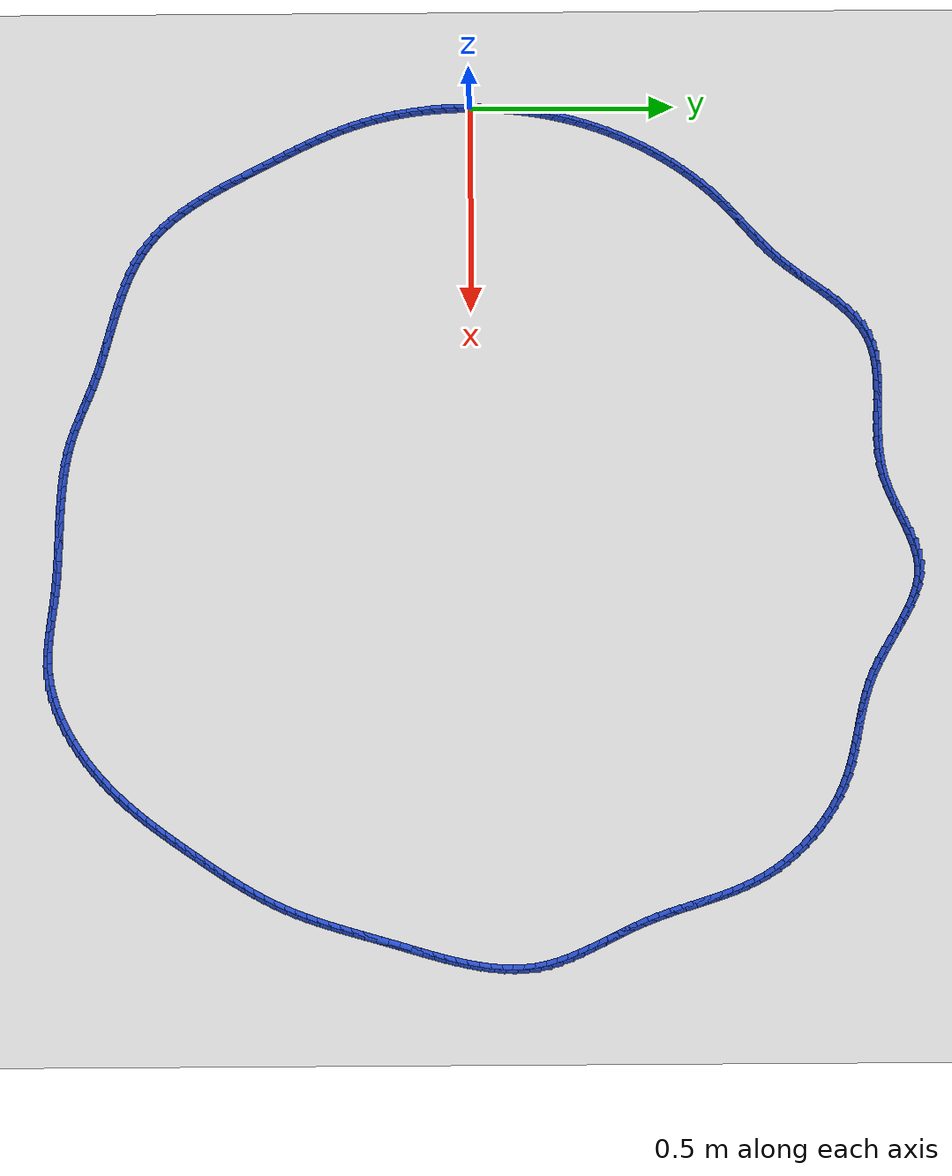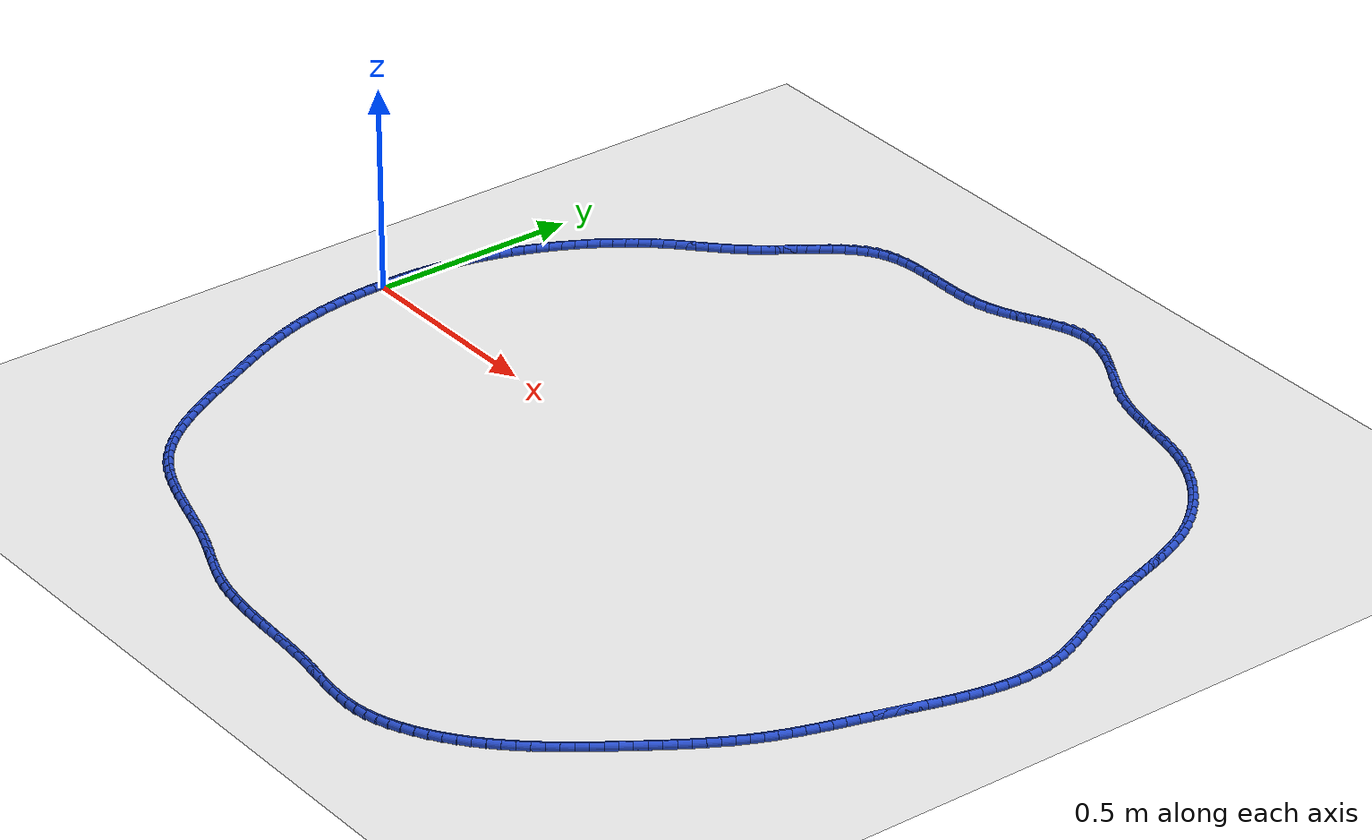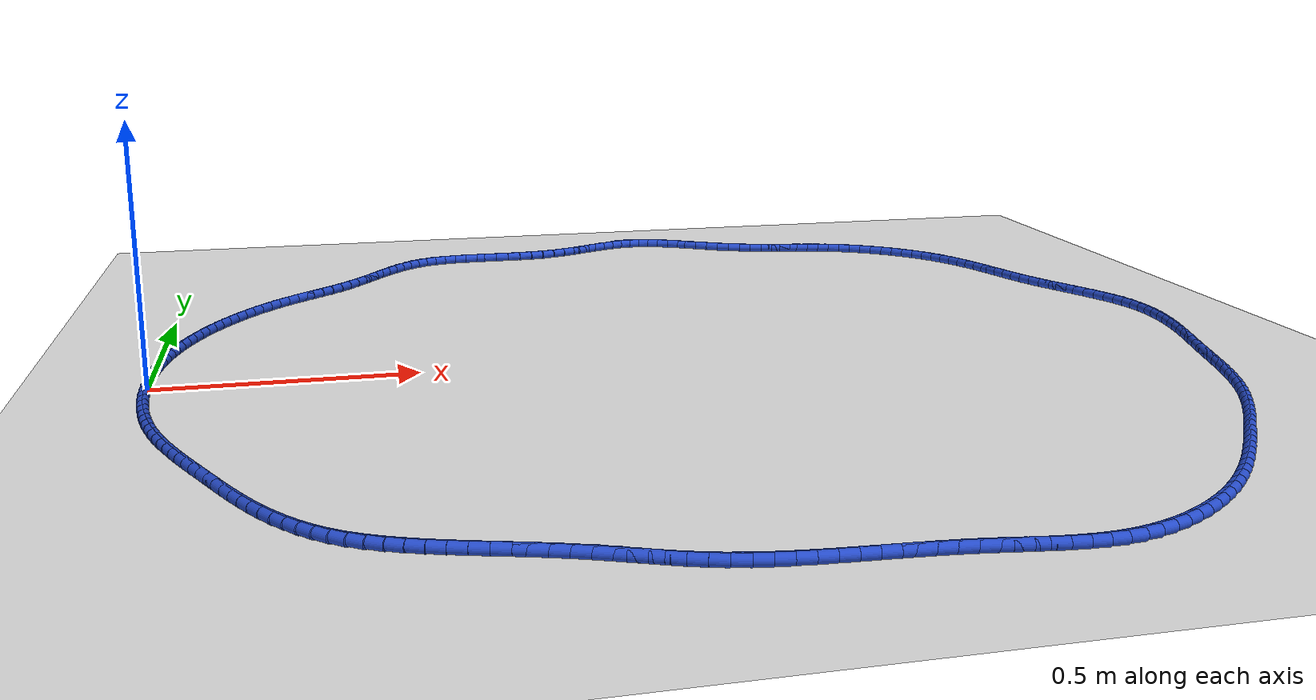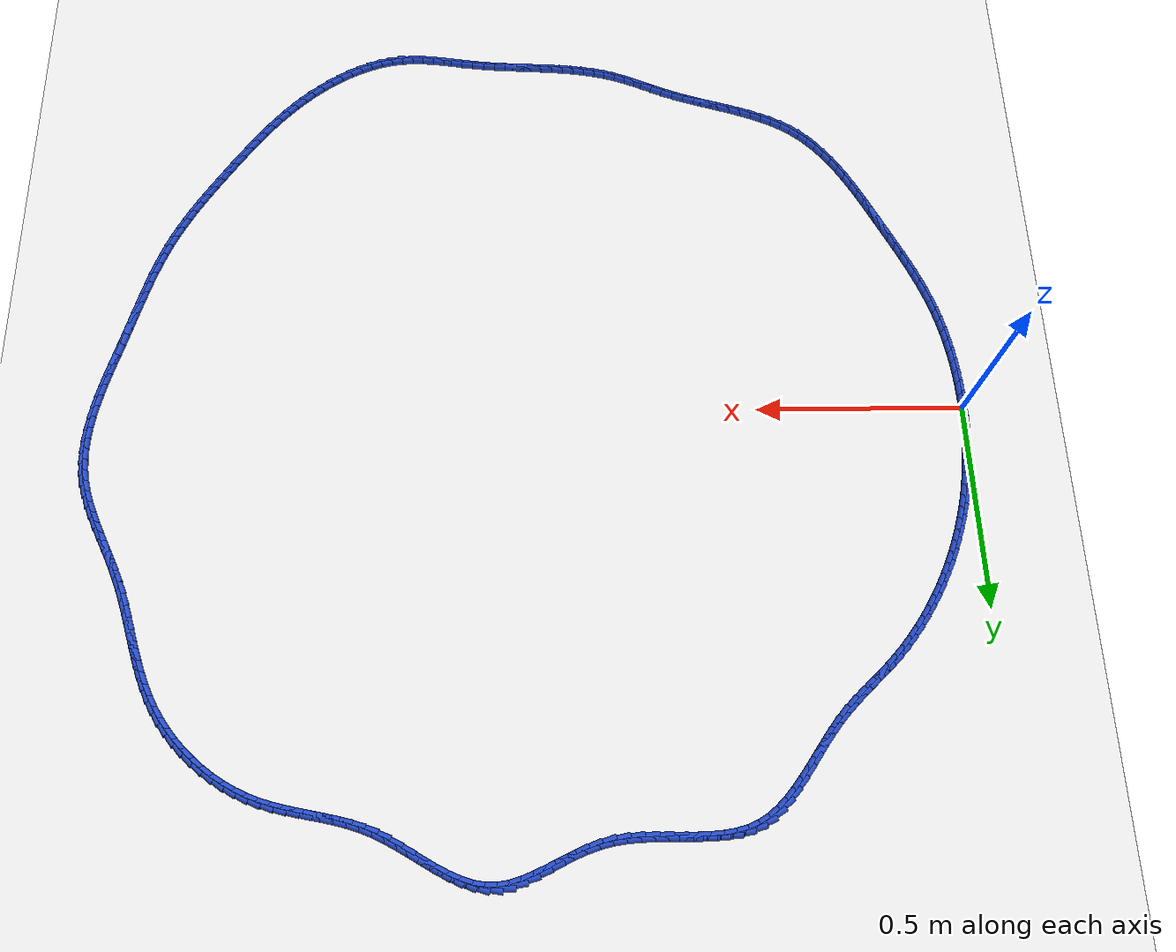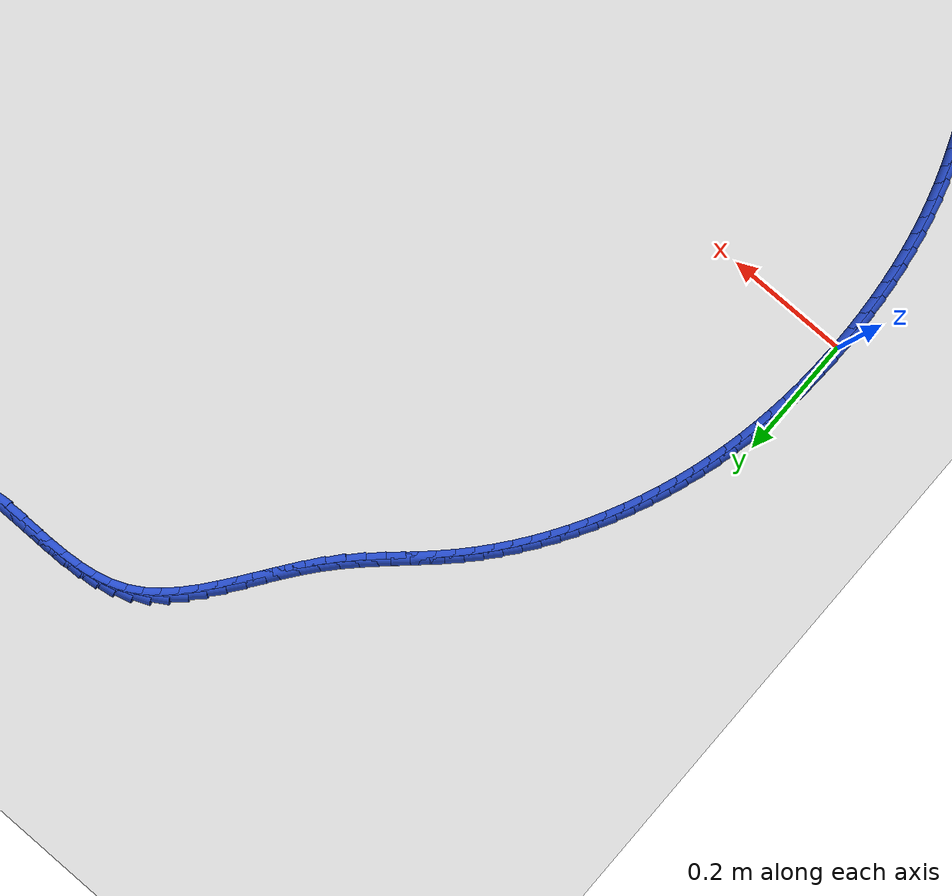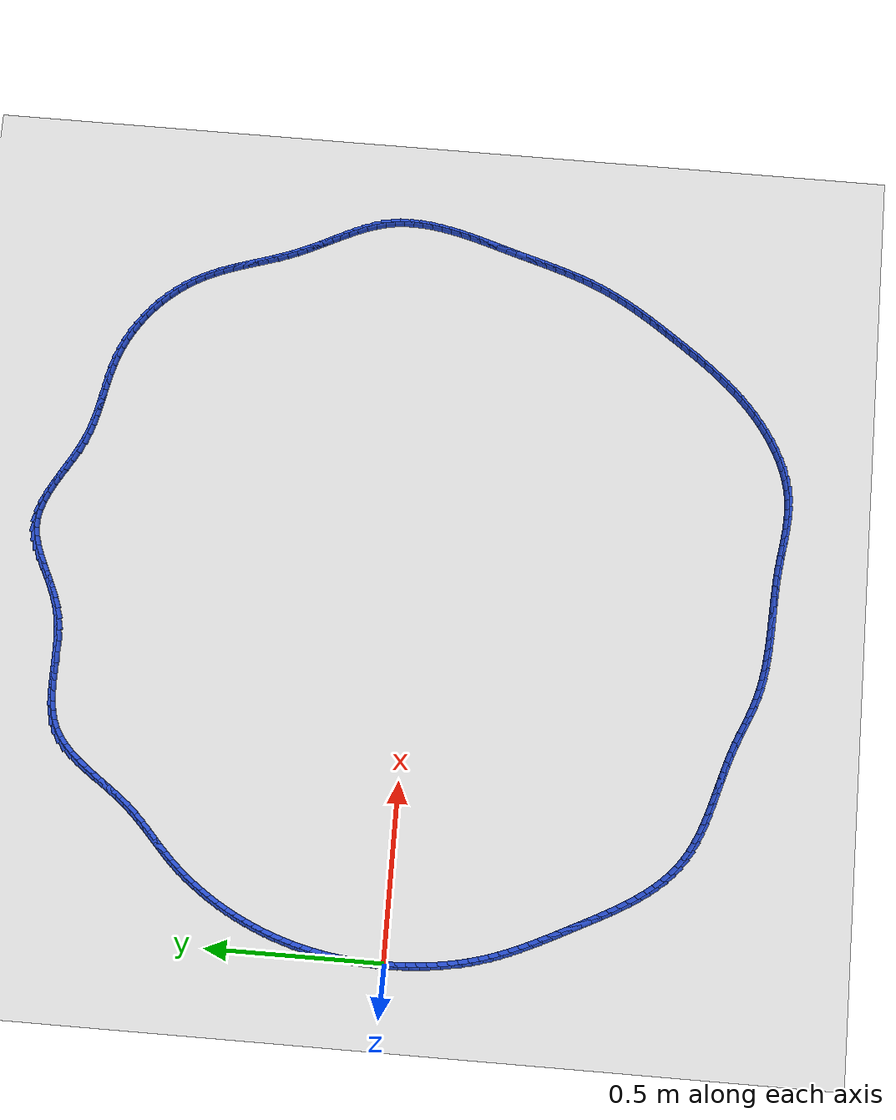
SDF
<sdf version="1.6">
 <world name="default">
  <light name="sun" type="directional">
   <pose>0 0 10 0 -0 0</pose>
   <diffuse>0.8 0.8 0.8 1</diffuse>
   <specular>0.2 0.2 0.2 1</specular>
   <attenuation>
    <range>1000</range>
    <constant>0.9</constant>
    <linear>0.01</linear>
    <quadratic>0.001</quadratic>
   </attenuation>
   <direction>-0.5 0.1 -0.9</direction>
  </light>
  <model name="ground_plane">
   <static>1</static>
   <link name="link">
    <collision name="collision">
     <geometry><plane><normal>0 0 1</normal><size>100 100</size></plane></geometry>
     <surface><friction><ode><mu>100</mu><mu2>50</mu2></ode></friction></surface>
    </collision>
    <visual name="visual">
     <cast_shadows>0</cast_shadows>
     <geometry><plane><normal>0 0 1</normal><size>100 100</size></plane></geometry>
     <material>
      <script><uri>file://media/materials/scripts/gazebo.material</uri><name>Gazebo/WhiteGlow</name></script>
     </material>
    </visual>
   </link>
  </model>
  <gravity>0 0 -9.8</gravity>
  <magnetic_field>6e-06 2.3e-05 -4.2e-05</magnetic_field>
  <atmosphere type="adiabatic"/>
  <physics name="default_physics" default="0" type="ode">
   <max_step_size>0.001</max_step_size>
   <real_time_factor>1</real_time_factor>
   <real_time_update_rate>1000</real_time_update_rate>
  </physics>
  <scene><ambient>0.4 0.4 0.4 1</ambient><background>0.7 0.7 0.7 1</background><shadows>1</shadows></scene>
  <spherical_coordinates>
   <surface_model>EARTH_WGS84</surface_model>
   <latitude_deg>0</latitude_deg>
   <longitude_deg>0</longitude_deg>
   <elevation>0</elevation>
   <heading_deg>0</heading_deg>
  </spherical_coordinates>
  <model name="line">
   <link name="link_0">
    <pose>-7.806255641895632e-18 6.938893903907228e-17 0.01 0 1.57 1.5565138516227055</pose>
    <collision name="collision">
     <geometry><cylinder><radius>0.01</radius><length>0.08</length></cylinder></geometry>
    </collision>
    <visual name="visual">
     <material>
      <script><name>Gazebo/Blue</name><uri>file://media/materials/scripts/gazebo.material</uri></script>
     </material>
     <geometry><cylinder><radius>0.01</radius><length>0.08</length></cylinder></geometry>
    </visual>
   </link>
   <link name="link_1">
    <pose>0.0004160577210864394 0.0291286646938342 0.01 0 1.57 1.529346896306358</pose>
    <collision name="collision">
     <geometry><cylinder><radius>0.01</radius><length>0.08</length></cylinder></geometry>
    </collision>
    <visual name="visual">
     <material>
      <script><name>Gazebo/Blue</name><uri>file://media/materials/scripts/gazebo.material</uri></script>
     </material>
     <geometry><cylinder><radius>0.01</radius><length>0.08</length></cylinder></geometry>
    </visual>
   </link>
   <link name="link_2">
    <pose>0.001621099598157107 0.05818459319023853 0.01 0 1.57 1.5013668621153997</pose>
    <collision name="collision">
     <geometry><cylinder><radius>0.01</radius><length>0.08</length></cylinder></geometry>
    </collision>
    <visual name="visual">
     <material>
      <script><name>Gazebo/Blue</name><uri>file://media/materials/scripts/gazebo.material</uri></script>
     </material>
     <geometry><cylinder><radius>0.01</radius><length>0.08</length></cylinder></geometry>
    </visual>
   </link>
   <link name="link_3">
    <pose>0.003635785614684991 0.08715569002295097 0.01 0 1.57 1.4725827064689223</pose>
    <collision name="collision">
     <geometry><cylinder><radius>0.01</radius><length>0.08</length></cylinder></geometry>
    </collision>
    <visual name="visual">
     <material>
      <script><name>Gazebo/Blue</name><uri>file://media/materials/scripts/gazebo.material</uri></script>
     </material>
     <geometry><cylinder><radius>0.01</radius><length>0.08</length></cylinder></geometry>
    </visual>
   </link>
   <link name="link_4">
    <pose>0.006480775754143074 0.1160298597257092 0.01 0 1.57 1.4430092325313042</pose>
    <collision name="collision">
     <geometry><cylinder><radius>0.01</radius><length>0.08</length></cylinder></geometry>
    </collision>
    <visual name="visual">
     <material>
      <script><name>Gazebo/Blue</name><uri>file://media/materials/scripts/gazebo.material</uri></script>
     </material>
     <geometry><cylinder><radius>0.01</radius><length>0.08</length></cylinder></geometry>
    </visual>
   </link>
   <link name="link_5">
    <pose>0.01017673000000435 0.14479500683225116 0.01 0 1.57 1.4126675801249295</pose>
    <collision name="collision">
     <geometry><cylinder><radius>0.01</radius><length>0.08</length></cylinder></geometry>
    </collision>
    <visual name="visual">
     <material>
      <script><name>Gazebo/Blue</name><uri>file://media/materials/scripts/gazebo.material</uri></script>
     </material>
     <geometry><cylinder><radius>0.01</radius><length>0.08</length></cylinder></geometry>
    </visual>
   </link>
   <link name="link_6">
    <pose>0.014744308335741817 0.1734390358763146 0.01 0 1.57 1.3815856474778683</pose>
    <collision name="collision">
     <geometry><cylinder><radius>0.01</radius><length>0.08</length></cylinder></geometry>
    </collision>
    <visual name="visual">
     <material>
      <script><name>Gazebo/Blue</name><uri>file://media/materials/scripts/gazebo.material</uri></script>
     </material>
     <geometry><cylinder><radius>0.01</radius><length>0.08</length></cylinder></geometry>
    </visual>
   </link>
   <link name="link_7">
    <pose>0.020204170744828453 0.20194985139163726 0.01 0 1.57 1.3497984178220863</pose>
    <collision name="collision">
     <geometry><cylinder><radius>0.01</radius><length>0.08</length></cylinder></geometry>
    </collision>
    <visual name="visual">
     <material>
      <script><name>Gazebo/Blue</name><uri>file://media/materials/scripts/gazebo.material</uri></script>
     </material>
     <geometry><cylinder><radius>0.01</radius><length>0.08</length></cylinder></geometry>
    </visual>
   </link>
   <link name="link_8">
    <pose>0.026576977210737256 0.23031535791195712 0.01 0 1.57 1.3173481644162899</pose>
    <collision name="collision">
     <geometry><cylinder><radius>0.01</radius><length>0.08</length></cylinder></geometry>
    </collision>
    <visual name="visual">
     <material>
      <script><name>Gazebo/Blue</name><uri>file://media/materials/scripts/gazebo.material</uri></script>
     </material>
     <geometry><cylinder><radius>0.01</radius><length>0.08</length></cylinder></geometry>
    </visual>
   </link>
   <link name="link_9">
    <pose>0.033883387716941216 0.25852345997101184 0.01 0 1.57 1.2843129945605964</pose>
    <collision name="collision">
     <geometry><cylinder><radius>0.01</radius><length>0.08</length></cylinder></geometry>
    </collision>
    <visual name="visual">
     <material>
      <script><name>Gazebo/Blue</name><uri>file://media/materials/scripts/gazebo.material</uri></script>
     </material>
     <geometry><cylinder><radius>0.01</radius><length>0.08</length></cylinder></geometry>
    </visual>
   </link>
   <link name="link_10">
    <pose>0.042142767172437375 0.28656061243632613 0.01 0 1.57 1.2511400645709698</pose>
    <collision name="collision">
     <geometry><cylinder><radius>0.01</radius><length>0.08</length></cylinder></geometry>
    </collision>
    <visual name="visual">
     <material>
      <script><name>Gazebo/Blue</name><uri>file://media/materials/scripts/gazebo.material</uri></script>
     </material>
     <geometry><cylinder><radius>0.01</radius><length>0.08</length></cylinder></geometry>
    </visual>
   </link>
   <link name="link_11">
    <pose>0.05135500116808042 0.31439146563067333 0.01 0 1.57 1.2180713739405626</pose>
    <collision name="collision">
     <geometry><cylinder><radius>0.01</radius><length>0.08</length></cylinder></geometry>
    </collision>
    <visual name="visual">
     <material>
      <script><name>Gazebo/Blue</name><uri>file://media/materials/scripts/gazebo.material</uri></script>
     </material>
     <geometry><cylinder><radius>0.01</radius><length>0.08</length></cylinder></geometry>
    </visual>
   </link>
   <link name="link_12">
    <pose>0.061504928166512374 0.34196382658805824 0.01 0 1.57 1.1850021355753138</pose>
    <collision name="collision">
     <geometry><cylinder><radius>0.01</radius><length>0.08</length></cylinder></geometry>
    </collision>
    <visual name="visual">
     <material>
      <script><name>Gazebo/Blue</name><uri>file://media/materials/scripts/gazebo.material</uri></script>
     </material>
     <geometry><cylinder><radius>0.01</radius><length>0.08</length></cylinder></geometry>
    </visual>
   </link>
   <link name="link_13">
    <pose>0.07257699655564943 0.36922506570493185 0.01 0 1.57 1.1518203462694694</pose>
    <collision name="collision">
     <geometry><cylinder><radius>0.01</radius><length>0.08</length></cylinder></geometry>
    </collision>
    <visual name="visual">
     <material>
      <script><name>Gazebo/Blue</name><uri>file://media/materials/scripts/gazebo.material</uri></script>
     </material>
     <geometry><cylinder><radius>0.01</radius><length>0.08</length></cylinder></geometry>
    </visual>
   </link>
   <link name="link_14">
    <pose>0.08455565472340792 0.3961225533777458 0.01 0 1.57 1.1184150258684533</pose>
    <collision name="collision">
     <geometry><cylinder><radius>0.01</radius><length>0.08</length></cylinder></geometry>
    </collision>
    <visual name="visual">
     <material>
      <script><name>Gazebo/Blue</name><uri>file://media/materials/scripts/gazebo.material</uri></script>
     </material>
     <geometry><cylinder><radius>0.01</radius><length>0.08</length></cylinder></geometry>
    </visual>
   </link>
   <link name="link_15">
    <pose>0.097425351057704 0.4226036600029512 0.01 0 1.57 1.0846759340122978</pose>
    <collision name="collision">
     <geometry><cylinder><radius>0.01</radius><length>0.08</length></cylinder></geometry>
    </collision>
    <visual name="visual">
     <material>
      <script><name>Gazebo/Blue</name><uri>file://media/materials/scripts/gazebo.material</uri></script>
     </material>
     <geometry><cylinder><radius>0.01</radius><length>0.08</length></cylinder></geometry>
    </visual>
   </link>
   <link name="link_16">
    <pose>0.11117053394645397 0.44861575597699943 0.01 0 1.57 1.0504933724274816</pose>
    <collision name="collision">
     <geometry><cylinder><radius>0.01</radius><length>0.08</length></cylinder></geometry>
    </collision>
    <visual name="visual">
     <material>
      <script><name>Gazebo/Blue</name><uri>file://media/materials/scripts/gazebo.material</uri></script>
     </material>
     <geometry><cylinder><radius>0.01</radius><length>0.08</length></cylinder></geometry>
    </visual>
   </link>
   <link name="link_17">
    <pose>0.12577565177757405 0.47410621169634165 0.01 0 1.57 1.015758102492224</pose>
    <collision name="collision">
     <geometry><cylinder><radius>0.01</radius><length>0.08</length></cylinder></geometry>
    </collision>
    <visual name="visual">
     <material>
      <script><name>Gazebo/Blue</name><uri>file://media/materials/scripts/gazebo.material</uri></script>
     </material>
     <geometry><cylinder><radius>0.01</radius><length>0.08</length></cylinder></geometry>
    </visual>
   </link>
   <link name="link_18">
    <pose>0.14122515293898044 0.4990223975574292 0.01 0 1.57 0.9803614112717358</pose>
    <collision name="collision">
     <geometry><cylinder><radius>0.01</radius><length>0.08</length></cylinder></geometry>
    </collision>
    <visual name="visual">
     <material>
      <script><name>Gazebo/Blue</name><uri>file://media/materials/scripts/gazebo.material</uri></script>
     </material>
     <geometry><cylinder><radius>0.01</radius><length>0.08</length></cylinder></geometry>
    </visual>
   </link>
   <link name="link_19">
    <pose>0.1575034858185894 0.5233116839567135 0.01 0 1.57 0.9441953635440624</pose>
    <collision name="collision">
     <geometry><cylinder><radius>0.01</radius><length>0.08</length></cylinder></geometry>
    </collision>
    <visual name="visual">
     <material>
      <script><name>Gazebo/Blue</name><uri>file://media/materials/scripts/gazebo.material</uri></script>
     </material>
     <geometry><cylinder><radius>0.01</radius><length>0.08</length></cylinder></geometry>
    </visual>
   </link>
   <link name="link_20">
    <pose>0.17459509880431726 0.5469214412906459 0.01 0 1.57 0.9071532820691521</pose>
    <collision name="collision">
     <geometry><cylinder><radius>0.01</radius><length>0.08</length></cylinder></geometry>
    </collision>
    <visual name="visual">
     <material>
      <script><name>Gazebo/Blue</name><uri>file://media/materials/scripts/gazebo.material</uri></script>
     </material>
     <geometry><cylinder><radius>0.01</radius><length>0.08</length></cylinder></geometry>
    </visual>
   </link>
   <link name="link_21">
    <pose>0.19248444028408013 0.5697990399556775 0.01 0 1.57 0.8691305028372828</pose>
    <collision name="collision">
     <geometry><cylinder><radius>0.01</radius><length>0.08</length></cylinder></geometry>
    </collision>
    <visual name="visual">
     <material>
      <script><name>Gazebo/Blue</name><uri>file://media/materials/scripts/gazebo.material</uri></script>
     </material>
     <geometry><cylinder><radius>0.01</radius><length>0.08</length></cylinder></geometry>
    </visual>
   </link>
   <link name="link_22">
    <pose>0.21115595864579434 0.5918918503482595 0.01 0 1.57 0.8300254553127776</pose>
    <collision name="collision">
     <geometry><cylinder><radius>0.01</radius><length>0.08</length></cylinder></geometry>
    </collision>
    <visual name="visual">
     <material>
      <script><name>Gazebo/Blue</name><uri>file://media/materials/scripts/gazebo.material</uri></script>
     </material>
     <geometry><cylinder><radius>0.01</radius><length>0.08</length></cylinder></geometry>
    </visual>
   </link>
   <link name="link_23">
    <pose>0.23059410227737615 0.6131472428648437 0.01 0 1.57 0.7911776008991813</pose>
    <collision name="collision">
     <geometry><cylinder><radius>0.01</radius><length>0.08</length></cylinder></geometry>
    </collision>
    <visual name="visual">
     <material>
      <script><name>Gazebo/Blue</name><uri>file://media/materials/scripts/gazebo.material</uri></script>
     </material>
     <geometry><cylinder><radius>0.01</radius><length>0.08</length></cylinder></geometry>
    </visual>
   </link>
   <link name="link_24">
    <pose>0.25076242883055533 0.6335500503623519 0.01 0 1.57 0.7627263812229939</pose>
    <collision name="collision">
     <geometry><cylinder><radius>0.01</radius><length>0.08</length></cylinder></geometry>
    </collision>
    <visual name="visual">
     <material>
      <script><name>Gazebo/Blue</name><uri>file://media/materials/scripts/gazebo.material</uri></script>
     </material>
     <geometry><cylinder><radius>0.01</radius><length>0.08</length></cylinder></geometry>
    </visual>
   </link>
   <link name="link_25">
    <pose>0.271478304459102 0.653347264635749 0.01 0 1.57 0.7492347336074365</pose>
    <collision name="collision">
     <geometry><cylinder><radius>0.01</radius><length>0.08</length></cylinder></geometry>
    </collision>
    <visual name="visual">
     <material>
      <script><name>Gazebo/Blue</name><uri>file://media/materials/scripts/gazebo.material</uri></script>
     </material>
     <geometry><cylinder><radius>0.01</radius><length>0.08</length></cylinder></geometry>
    </visual>
   </link>
   <link name="link_26">
    <pose>0.29249664988567936 0.6728978581911434 0.01 0 1.57 0.7507489183592908</pose>
    <collision name="collision">
     <geometry><cylinder><radius>0.01</radius><length>0.08</length></cylinder></geometry>
    </collision>
    <visual name="visual">
     <material>
      <script><name>Gazebo/Blue</name><uri>file://media/materials/scripts/gazebo.material</uri></script>
     </material>
     <geometry><cylinder><radius>0.01</radius><length>0.08</length></cylinder></geometry>
    </visual>
   </link>
   <link name="link_27">
    <pose>0.31357215153824736 0.6925612236852772 0.01 0 1.57 0.7670735073424142</pose>
    <collision name="collision">
     <geometry><cylinder><radius>0.01</radius><length>0.08</length></cylinder></geometry>
    </collision>
    <visual name="visual">
     <material>
      <script><name>Gazebo/Blue</name><uri>file://media/materials/scripts/gazebo.material</uri></script>
     </material>
     <geometry><cylinder><radius>0.01</radius><length>0.08</length></cylinder></geometry>
    </visual>
   </link>
   <link name="link_28">
    <pose>0.3344594958447658 0.7126967537748917 0.01 0 1.57 0.7977877285938565</pose>
    <collision name="collision">
     <geometry><cylinder><radius>0.01</radius><length>0.08</length></cylinder></geometry>
    </collision>
    <visual name="visual">
     <material>
      <script><name>Gazebo/Blue</name><uri>file://media/materials/scripts/gazebo.material</uri></script>
     </material>
     <geometry><cylinder><radius>0.01</radius><length>0.08</length></cylinder></geometry>
    </visual>
   </link>
   <link name="link_29">
    <pose>0.3549133692331948 0.733663841116729 0.01 0 1.57 0.8421633521934188</pose>
    <collision name="collision">
     <geometry><cylinder><radius>0.01</radius><length>0.08</length></cylinder></geometry>
    </collision>
    <visual name="visual">
     <material>
      <script><name>Gazebo/Blue</name><uri>file://media/materials/scripts/gazebo.material</uri></script>
     </material>
     <geometry><cylinder><radius>0.01</radius><length>0.08</length></cylinder></geometry>
    </visual>
   </link>
   <link name="link_30">
    <pose>0.3746884753688165 0.7558218483637996 0.01 0 1.57 0.8928625279495159</pose>
    <collision name="collision">
     <geometry><cylinder><radius>0.01</radius><length>0.08</length></cylinder></geometry>
    </collision>
    <visual name="visual">
     <material>
      <script><name>Gazebo/Blue</name><uri>file://media/materials/scripts/gazebo.material</uri></script>
     </material>
     <geometry><cylinder><radius>0.01</radius><length>0.08</length></cylinder></geometry>
    </visual>
   </link>
   <link name="link_31">
    <pose>0.39363947091818535 0.7793561573711487 0.01 0 1.57 0.9290617429577055</pose>
    <collision name="collision">
     <geometry><cylinder><radius>0.01</radius><length>0.08</length></cylinder></geometry>
    </collision>
    <visual name="visual">
     <material>
      <script><name>Gazebo/Blue</name><uri>file://media/materials/scripts/gazebo.material</uri></script>
     </material>
     <geometry><cylinder><radius>0.01</radius><length>0.08</length></cylinder></geometry>
    </visual>
   </link>
   <link name="link_32">
    <pose>0.41195625145768466 0.8038686244138229 0.01 0 1.57 0.9477217719095651</pose>
    <collision name="collision">
     <geometry><cylinder><radius>0.01</radius><length>0.08</length></cylinder></geometry>
    </collision>
    <visual name="visual">
     <material>
      <script><name>Gazebo/Blue</name><uri>file://media/materials/scripts/gazebo.material</uri></script>
     </material>
     <geometry><cylinder><radius>0.01</radius><length>0.08</length></cylinder></geometry>
    </visual>
   </link>
   <link name="link_33">
    <pose>0.4298989168282309 0.8288389063950776 0.01 0 1.57 0.9495533548428046</pose>
    <collision name="collision">
     <geometry><cylinder><radius>0.01</radius><length>0.08</length></cylinder></geometry>
    </collision>
    <visual name="visual">
     <material>
      <script><name>Gazebo/Blue</name><uri>file://media/materials/scripts/gazebo.material</uri></script>
     </material>
     <geometry><cylinder><radius>0.01</radius><length>0.08</length></cylinder></geometry>
    </visual>
   </link>
   <link name="link_34">
    <pose>0.44772756687074067 0.8537466602181686 0.01 0 1.57 0.9344084621459418</pose>
    <collision name="collision">
     <geometry><cylinder><radius>0.01</radius><length>0.08</length></cylinder></geometry>
    </collision>
    <visual name="visual">
     <material>
      <script><name>Gazebo/Blue</name><uri>file://media/materials/scripts/gazebo.material</uri></script>
     </material>
     <geometry><cylinder><radius>0.01</radius><length>0.08</length></cylinder></geometry>
    </visual>
   </link>
   <link name="link_35">
    <pose>0.4657023014261307 0.8780715427863516 0.01 0 1.57 0.9012342017211799</pose>
    <collision name="collision">
     <geometry><cylinder><radius>0.01</radius><length>0.08</length></cylinder></geometry>
    </collision>
    <visual name="visual">
     <material>
      <script><name>Gazebo/Blue</name><uri>file://media/materials/scripts/gazebo.material</uri></script>
     </material>
     <geometry><cylinder><radius>0.01</radius><length>0.08</length></cylinder></geometry>
    </visual>
   </link>
   <link name="link_36">
    <pose>0.4840832203353177 0.9012932110028824 0.01 0 1.57 0.8480761478310571</pose>
    <collision name="collision">
     <geometry><cylinder><radius>0.01</radius><length>0.08</length></cylinder></geometry>
    </collision>
    <visual name="visual">
     <material>
      <script><name>Gazebo/Blue</name><uri>file://media/materials/scripts/gazebo.material</uri></script>
     </material>
     <geometry><cylinder><radius>0.01</radius><length>0.08</length></cylinder></geometry>
    </visual>
   </link>
   <link name="link_37">
    <pose>0.5031304234392181 0.9228913217710164 0.01 0 1.57 0.7722260636885259</pose>
    <collision name="collision">
     <geometry><cylinder><radius>0.01</radius><length>0.08</length></cylinder></geometry>
    </collision>
    <visual name="visual">
     <material>
      <script><name>Gazebo/Blue</name><uri>file://media/materials/scripts/gazebo.material</uri></script>
     </material>
     <geometry><cylinder><radius>0.01</radius><length>0.08</length></cylinder></geometry>
    </visual>
   </link>
   <link name="link_38">
    <pose>0.5231040105787488 0.9423455319940099 0.01 0 1.57 0.6707489983790816</pose>
    <collision name="collision">
     <geometry><cylinder><radius>0.01</radius><length>0.08</length></cylinder></geometry>
    </collision>
    <visual name="visual">
     <material>
      <script><name>Gazebo/Blue</name><uri>file://media/materials/scripts/gazebo.material</uri></script>
     </material>
     <geometry><cylinder><radius>0.01</radius><length>0.08</length></cylinder></geometry>
    </visual>
   </link>
   <link name="link_39">
    <pose>0.5442640815948264 0.9591354985751186 0.01 0 1.57 0.541764548540065</pose>
    <collision name="collision">
     <geometry><cylinder><radius>0.01</radius><length>0.08</length></cylinder></geometry>
    </collision>
    <visual name="visual">
     <material>
      <script><name>Gazebo/Blue</name><uri>file://media/materials/scripts/gazebo.material</uri></script>
     </material>
     <geometry><cylinder><radius>0.01</radius><length>0.08</length></cylinder></geometry>
    </visual>
   </link>
   <link name="link_40">
    <pose>0.5668707363283675 0.9727408784175975 0.01 0 1.57 0.3934134070438369</pose>
    <collision name="collision">
     <geometry><cylinder><radius>0.01</radius><length>0.08</length></cylinder></geometry>
    </collision>
    <visual name="visual">
     <material>
      <script><name>Gazebo/Blue</name><uri>file://media/materials/scripts/gazebo.material</uri></script>
     </material>
     <geometry><cylinder><radius>0.01</radius><length>0.08</length></cylinder></geometry>
    </visual>
   </link>
   <link name="link_41">
    <pose>0.5911152631262181 0.9828035861006209 0.01 0 1.57 0.26153164379875293</pose>
    <collision name="collision">
     <geometry><cylinder><radius>0.01</radius><length>0.08</length></cylinder></geometry>
    </collision>
    <visual name="visual">
     <material>
      <script><name>Gazebo/Blue</name><uri>file://media/materials/scripts/gazebo.material</uri></script>
     </material>
     <geometry><cylinder><radius>0.01</radius><length>0.08</length></cylinder></geometry>
    </visual>
   </link>
   <link name="link_42">
    <pose>0.6168777942477184 0.9896992430395262 0.01 0 1.57 0.15793028334962045</pose>
    <collision name="collision">
     <geometry><cylinder><radius>0.01</radius><length>0.08</length></cylinder></geometry>
    </collision>
    <visual name="visual">
     <material>
      <script><name>Gazebo/Blue</name><uri>file://media/materials/scripts/gazebo.material</uri></script>
     </material>
     <geometry><cylinder><radius>0.01</radius><length>0.08</length></cylinder></geometry>
    </visual>
   </link>
   <link name="link_43">
    <pose>0.6439505542083239 0.9940107573306136 0.01 0 1.57 0.08181431172003366</pose>
    <collision name="collision">
     <geometry><cylinder><radius>0.01</radius><length>0.08</length></cylinder></geometry>
    </collision>
    <visual name="visual">
     <material>
      <script><name>Gazebo/Blue</name><uri>file://media/materials/scripts/gazebo.material</uri></script>
     </material>
     <geometry><cylinder><radius>0.01</radius><length>0.08</length></cylinder></geometry>
    </visual>
   </link>
   <link name="link_44">
    <pose>0.672125762212844 0.9963210495926981 0.01 0 1.57 0.030674746850218437</pose>
    <collision name="collision">
     <geometry><cylinder><radius>0.01</radius><length>0.08</length></cylinder></geometry>
    </collision>
    <visual name="visual">
     <material>
      <script><name>Gazebo/Blue</name><uri>file://media/materials/scripts/gazebo.material</uri></script>
     </material>
     <geometry><cylinder><radius>0.01</radius><length>0.08</length></cylinder></geometry>
    </visual>
   </link>
   <link name="link_45">
    <pose>0.7011956374660886 0.9972130404445956 0.01 0 1.57 0.0019024244905861557</pose>
    <collision name="collision">
     <geometry><cylinder><radius>0.01</radius><length>0.08</length></cylinder></geometry>
    </collision>
    <visual name="visual">
     <material>
      <script><name>Gazebo/Blue</name><uri>file://media/materials/scripts/gazebo.material</uri></script>
     </material>
     <geometry><cylinder><radius>0.01</radius><length>0.08</length></cylinder></geometry>
    </visual>
   </link>
   <link name="link_46">
    <pose>0.7309523991728674 0.9972696505051218 0.01 0 1.57 -0.006477319491099967</pose>
    <collision name="collision">
     <geometry><cylinder><radius>0.01</radius><length>0.08</length></cylinder></geometry>
    </collision>
    <visual name="visual">
     <material>
      <script><name>Gazebo/Blue</name><uri>file://media/materials/scripts/gazebo.material</uri></script>
     </material>
     <geometry><cylinder><radius>0.01</radius><length>0.08</length></cylinder></geometry>
    </visual>
   </link>
   <link name="link_47">
    <pose>0.7611882665379898 0.9970738003930923 0.01 0 1.57 0.004412384451497344</pose>
    <collision name="collision">
     <geometry><cylinder><radius>0.01</radius><length>0.08</length></cylinder></geometry>
    </collision>
    <visual name="visual">
     <material>
      <script><name>Gazebo/Blue</name><uri>file://media/materials/scripts/gazebo.material</uri></script>
     </material>
     <geometry><cylinder><radius>0.01</radius><length>0.08</length></cylinder></geometry>
    </visual>
   </link>
   <link name="link_48">
    <pose>0.7916954587662657 0.9972084107273227 0.01 0 1.57 0.034267449527861454</pose>
    <collision name="collision">
     <geometry><cylinder><radius>0.01</radius><length>0.08</length></cylinder></geometry>
    </collision>
    <visual name="visual">
     <material>
      <script><name>Gazebo/Blue</name><uri>file://media/materials/scripts/gazebo.material</uri></script>
     </material>
     <geometry><cylinder><radius>0.01</radius><length>0.08</length></cylinder></geometry>
    </visual>
   </link>
   <link name="link_49">
    <pose>0.8222661950625043 0.9982564021266284 0.01 0 1.57 0.08342686745658927</pose>
    <collision name="collision">
     <geometry><cylinder><radius>0.01</radius><length>0.08</length></cylinder></geometry>
    </collision>
    <visual name="visual">
     <material>
      <script><name>Gazebo/Blue</name><uri>file://media/materials/scripts/gazebo.material</uri></script>
     </material>
     <geometry><cylinder><radius>0.01</radius><length>0.08</length></cylinder></geometry>
    </visual>
   </link>
   <link name="link_50">
    <pose>0.8526926946315159 1.0008006952098252 0.01 0 1.57 0.15254122638977816</pose>
    <collision name="collision">
     <geometry><cylinder><radius>0.01</radius><length>0.08</length></cylinder></geometry>
    </collision>
    <visual name="visual">
     <material>
      <script><name>Gazebo/Blue</name><uri>file://media/materials/scripts/gazebo.material</uri></script>
     </material>
     <geometry><cylinder><radius>0.01</radius><length>0.08</length></cylinder></geometry>
    </visual>
   </link>
   <link name="link_51">
    <pose>0.8827671766781098 1.0054242105957287 0.01 0 1.57 0.24185025175334954</pose>
    <collision name="collision">
     <geometry><cylinder><radius>0.01</radius><length>0.08</length></cylinder></geometry>
    </collision>
    <visual name="visual">
     <material>
      <script><name>Gazebo/Blue</name><uri>file://media/materials/scripts/gazebo.material</uri></script>
     </material>
     <geometry><cylinder><radius>0.01</radius><length>0.08</length></cylinder></geometry>
    </visual>
   </link>
   <link name="link_52">
    <pose>0.9122827681071964 1.012705076835079 0.01 0 1.57 0.3345268677731419</pose>
    <collision name="collision">
     <geometry><cylinder><radius>0.01</radius><length>0.08</length></cylinder></geometry>
    </collision>
    <visual name="visual">
     <material>
      <script><name>Gazebo/Blue</name><uri>file://media/materials/scripts/gazebo.material</uri></script>
     </material>
     <geometry><cylinder><radius>0.01</radius><length>0.08</length></cylinder></geometry>
    </visual>
   </link>
   <link name="link_53">
    <pose>0.9411255720701204 1.0227305681733172 0.01 0 1.57 0.4004153501430796</pose>
    <collision name="collision">
     <geometry><cylinder><radius>0.01</radius><length>0.08</length></cylinder></geometry>
    </collision>
    <visual name="visual">
     <material>
      <script><name>Gazebo/Blue</name><uri>file://media/materials/scripts/gazebo.material</uri></script>
     </material>
     <geometry><cylinder><radius>0.01</radius><length>0.08</length></cylinder></geometry>
    </visual>
   </link>
   <link name="link_54">
    <pose>0.9693538428466659 1.0346791125021453 0.01 0 1.57 0.43749431682647677</pose>
    <collision name="collision">
     <geometry><cylinder><radius>0.01</radius><length>0.08</length></cylinder></geometry>
    </collision>
    <visual name="visual">
     <material>
      <script><name>Gazebo/Blue</name><uri>file://media/materials/scripts/gazebo.material</uri></script>
     </material>
     <geometry><cylinder><radius>0.01</radius><length>0.08</length></cylinder></geometry>
    </visual>
   </link>
   <link name="link_55">
    <pose>0.9970444868870406 1.0476306663455053 0.01 0 1.57 0.4464495881723244</pose>
    <collision name="collision">
     <geometry><cylinder><radius>0.01</radius><length>0.08</length></cylinder></geometry>
    </collision>
    <visual name="visual">
     <material>
      <script><name>Gazebo/Blue</name><uri>file://media/materials/scripts/gazebo.material</uri></script>
     </material>
     <geometry><cylinder><radius>0.01</radius><length>0.08</length></cylinder></geometry>
    </visual>
   </link>
   <link name="link_56">
    <pose>1.0242744106414514 1.0606651862273395 0.01 0 1.57 0.4264627902786795</pose>
    <collision name="collision">
     <geometry><cylinder><radius>0.01</radius><length>0.08</length></cylinder></geometry>
    </collision>
    <visual name="visual">
     <material>
      <script><name>Gazebo/Blue</name><uri>file://media/materials/scripts/gazebo.material</uri></script>
     </material>
     <geometry><cylinder><radius>0.01</radius><length>0.08</length></cylinder></geometry>
    </visual>
   </link>
   <link name="link_57">
    <pose>1.0511205205601066 1.07286262867159 0.01 0 1.57 0.37479725496185</pose>
    <collision name="collision">
     <geometry><cylinder><radius>0.01</radius><length>0.08</length></cylinder></geometry>
    </collision>
    <visual name="visual">
     <material>
      <script><name>Gazebo/Blue</name><uri>file://media/materials/scripts/gazebo.material</uri></script>
     </material>
     <geometry><cylinder><radius>0.01</radius><length>0.08</length></cylinder></geometry>
    </visual>
   </link>
   <link name="link_58">
    <pose>1.0776597230932128 1.0833029502021994 0.01 0 1.57 0.28693127661629986</pose>
    <collision name="collision">
     <geometry><cylinder><radius>0.01</radius><length>0.08</length></cylinder></geometry>
    </collision>
    <visual name="visual">
     <material>
      <script><name>Gazebo/Blue</name><uri>file://media/materials/scripts/gazebo.material</uri></script>
     </material>
     <geometry><cylinder><radius>0.01</radius><length>0.08</length></cylinder></geometry>
    </visual>
   </link>
   <link name="link_59">
    <pose>1.1039689246909783 1.0910661073431103 0.01 0 1.57 0.15794586720518042</pose>
    <collision name="collision">
     <geometry><cylinder><radius>0.01</radius><length>0.08</length></cylinder></geometry>
    </collision>
    <visual name="visual">
     <material>
      <script><name>Gazebo/Blue</name><uri>file://media/materials/scripts/gazebo.material</uri></script>
     </material>
     <geometry><cylinder><radius>0.01</radius><length>0.08</length></cylinder></geometry>
    </visual>
   </link>
   <link name="link_60">
    <pose>1.1301250318036102 1.0952320566182643 0.01 0 1.57 -0.011005733709864168</pose>
    <collision name="collision">
     <geometry><cylinder><radius>0.01</radius><length>0.08</length></cylinder></geometry>
    </collision>
    <visual name="visual">
     <material>
      <script><name>Gazebo/Blue</name><uri>file://media/materials/scripts/gazebo.material</uri></script>
     </material>
     <geometry><cylinder><radius>0.01</radius><length>0.08</length></cylinder></geometry>
    </visual>
   </link>
   <link name="link_61">
    <pose>1.156203605078673 1.0949450311964084 0.01 0 1.57 -0.1778721566792667</pose>
    <collision name="collision">
     <geometry><cylinder><radius>0.01</radius><length>0.08</length></cylinder></geometry>
    </collision>
    <visual name="visual">
     <material>
      <script><name>Gazebo/Blue</name><uri>file://media/materials/scripts/gazebo.material</uri></script>
     </material>
     <geometry><cylinder><radius>0.01</radius><length>0.08</length></cylinder></geometry>
    </visual>
   </link>
   <link name="link_62">
    <pose>1.182261123567059 1.0902606170497673 0.01 0 1.57 -0.30985496292280185</pose>
    <collision name="collision">
     <geometry><cylinder><radius>0.01</radius><length>0.08</length></cylinder></geometry>
    </collision>
    <visual name="visual">
     <material>
      <script><name>Gazebo/Blue</name><uri>file://media/materials/scripts/gazebo.material</uri></script>
     </material>
     <geometry><cylinder><radius>0.01</radius><length>0.08</length></cylinder></geometry>
    </visual>
   </link>
   <link name="link_63">
    <pose>1.2083398990999827 1.0819110382533577 0.01 0 1.57 -0.40691875857529447</pose>
    <collision name="collision">
     <geometry><cylinder><radius>0.01</radius><length>0.08</length></cylinder></geometry>
    </collision>
    <visual name="visual">
     <material>
      <script><name>Gazebo/Blue</name><uri>file://media/materials/scripts/gazebo.material</uri></script>
     </material>
     <geometry><cylinder><radius>0.01</radius><length>0.08</length></cylinder></geometry>
    </visual>
   </link>
   <link name="link_64">
    <pose>1.2344819079861373 1.070644543714735 0.01 0 1.57 -0.47309838166674767</pose>
    <collision name="collision">
     <geometry><cylinder><radius>0.01</radius><length>0.08</length></cylinder></geometry>
    </collision>
    <visual name="visual">
     <material>
      <script><name>Gazebo/Blue</name><uri>file://media/materials/scripts/gazebo.material</uri></script>
     </material>
     <geometry><cylinder><radius>0.01</radius><length>0.08</length></cylinder></geometry>
    </visual>
   </link>
   <link name="link_65">
    <pose>1.2607291265342149 1.0572093823414515 0.01 0 1.57 -0.5126405852235926</pose>
    <collision name="collision">
     <geometry><cylinder><radius>0.01</radius><length>0.08</length></cylinder></geometry>
    </collision>
    <visual name="visual">
     <material>
      <script><name>Gazebo/Blue</name><uri>file://media/materials/scripts/gazebo.material</uri></script>
     </material>
     <geometry><cylinder><radius>0.01</radius><length>0.08</length></cylinder></geometry>
    </visual>
   </link>
   <link name="link_66">
    <pose>1.2871235310529077 1.0423538030410615 0.01 0 1.57 -0.5286543267103231</pose>
    <collision name="collision">
     <geometry><cylinder><radius>0.01</radius><length>0.08</length></cylinder></geometry>
    </collision>
    <visual name="visual">
     <material>
      <script><name>Gazebo/Blue</name><uri>file://media/materials/scripts/gazebo.material</uri></script>
     </material>
     <geometry><cylinder><radius>0.01</radius><length>0.08</length></cylinder></geometry>
    </visual>
   </link>
   <link name="link_67">
    <pose>1.3137070978509087 1.026826054721119 0.01 0 1.57 -0.5227646263104361</pose>
    <collision name="collision">
     <geometry><cylinder><radius>0.01</radius><length>0.08</length></cylinder></geometry>
    </collision>
    <visual name="visual">
     <material>
      <script><name>Gazebo/Blue</name><uri>file://media/materials/scripts/gazebo.material</uri></script>
     </material>
     <geometry><cylinder><radius>0.01</radius><length>0.08</length></cylinder></geometry>
    </visual>
   </link>
   <link name="link_68">
    <pose>1.3405218032369104 1.0113743862891773 0.01 0 1.57 -0.49513088209074785</pose>
    <collision name="collision">
     <geometry><cylinder><radius>0.01</radius><length>0.08</length></cylinder></geometry>
    </collision>
    <visual name="visual">
     <material>
      <script><name>Gazebo/Blue</name><uri>file://media/materials/scripts/gazebo.material</uri></script>
     </material>
     <geometry><cylinder><radius>0.01</radius><length>0.08</length></cylinder></geometry>
    </visual>
   </link>
   <link name="link_69">
    <pose>1.3676096235196056 0.9967470466527906 0.01 0 1.57 -0.44459043400425724</pose>
    <collision name="collision">
     <geometry><cylinder><radius>0.01</radius><length>0.08</length></cylinder></geometry>
    </collision>
    <visual name="visual">
     <material>
      <script><name>Gazebo/Blue</name><uri>file://media/materials/scripts/gazebo.material</uri></script>
     </material>
     <geometry><cylinder><radius>0.01</radius><length>0.08</length></cylinder></geometry>
    </visual>
   </link>
   <link name="link_70">
    <pose>1.3950125350076865 0.9836922847195123 0.01 0 1.57 -0.37318777301353545</pose>
    <collision name="collision">
     <geometry><cylinder><radius>0.01</radius><length>0.08</length></cylinder></geometry>
    </collision>
    <visual name="visual">
     <material>
      <script><name>Gazebo/Blue</name><uri>file://media/materials/scripts/gazebo.material</uri></script>
     </material>
     <geometry><cylinder><radius>0.01</radius><length>0.08</length></cylinder></geometry>
    </visual>
   </link>
   <link name="link_71">
    <pose>1.4227585056422307 0.9728287647541558 0.01 0 1.57 -0.30600332045393325</pose>
    <collision name="collision">
     <geometry><cylinder><radius>0.01</radius><length>0.08</length></cylinder></geometry>
    </collision>
    <visual name="visual">
     <material>
      <script><name>Gazebo/Blue</name><uri>file://media/materials/scripts/gazebo.material</uri></script>
     </material>
     <geometry><cylinder><radius>0.01</radius><length>0.08</length></cylinder></geometry>
    </visual>
   </link>
   <link name="link_72">
    <pose>1.4507888163502038 0.9639732513239286 0.01 0 1.57 -0.2543410759152054</pose>
    <collision name="collision">
     <geometry><cylinder><radius>0.01</radius><length>0.08</length></cylinder></geometry>
    </collision>
    <visual name="visual">
     <material>
      <script><name>Gazebo/Blue</name><uri>file://media/materials/scripts/gazebo.material</uri></script>
     </material>
     <geometry><cylinder><radius>0.01</radius><length>0.08</length></cylinder></geometry>
    </visual>
   </link>
   <link name="link_73">
    <pose>1.4790116282064136 0.9566361332406801 0.01 0 1.57 -0.21916873059317224</pose>
    <collision name="collision">
     <geometry><cylinder><radius>0.01</radius><length>0.08</length></cylinder></geometry>
    </collision>
    <visual name="visual">
     <material>
      <script><name>Gazebo/Blue</name><uri>file://media/materials/scripts/gazebo.material</uri></script>
     </material>
     <geometry><cylinder><radius>0.01</radius><length>0.08</length></cylinder></geometry>
    </visual>
   </link>
   <link name="link_74">
    <pose>1.5073350360190434 0.9503271863157113 0.01 0 1.57 -0.20094228515973792</pose>
    <collision name="collision">
     <geometry><cylinder><radius>0.01</radius><length>0.08</length></cylinder></geometry>
    </collision>
    <visual name="visual">
     <material>
      <script><name>Gazebo/Blue</name><uri>file://media/materials/scripts/gazebo.material</uri></script>
     </material>
     <geometry><cylinder><radius>0.01</radius><length>0.08</length></cylinder></geometry>
    </visual>
   </link>
   <link name="link_75">
    <pose>1.5356671345962758 0.9445561863603242 0.01 0 1.57 -0.19989611583409328</pose>
    <collision name="collision">
     <geometry><cylinder><radius>0.01</radius><length>0.08</length></cylinder></geometry>
    </collision>
    <visual name="visual">
     <material>
      <script><name>Gazebo/Blue</name><uri>file://media/materials/scripts/gazebo.material</uri></script>
     </material>
     <geometry><cylinder><radius>0.01</radius><length>0.08</length></cylinder></geometry>
    </visual>
   </link>
   <link name="link_76">
    <pose>1.5639160187462942 0.9388329091858204 0.01 0 1.57 -0.21619524108455884</pose>
    <collision name="collision">
     <geometry><cylinder><radius>0.01</radius><length>0.08</length></cylinder></geometry>
    </collision>
    <visual name="visual">
     <material>
      <script><name>Gazebo/Blue</name><uri>file://media/materials/scripts/gazebo.material</uri></script>
     </material>
     <geometry><cylinder><radius>0.01</radius><length>0.08</length></cylinder></geometry>
    </visual>
   </link>
   <link name="link_77">
    <pose>1.591989783277281 0.932667130603501 0.01 0 1.57 -0.24994185665946878</pose>
    <collision name="collision">
     <geometry><cylinder><radius>0.01</radius><length>0.08</length></cylinder></geometry>
    </collision>
    <visual name="visual">
     <material>
      <script><name>Gazebo/Blue</name><uri>file://media/materials/scripts/gazebo.material</uri></script>
     </material>
     <geometry><cylinder><radius>0.01</radius><length>0.08</length></cylinder></geometry>
    </visual>
   </link>
   <link name="link_78">
    <pose>1.6197965229974192 0.9255686264246678 0.01 0 1.57 -0.3010255164171406</pose>
    <collision name="collision">
     <geometry><cylinder><radius>0.01</radius><length>0.08</length></cylinder></geometry>
    </collision>
    <visual name="visual">
     <material>
      <script><name>Gazebo/Blue</name><uri>file://media/materials/scripts/gazebo.material</uri></script>
     </material>
     <geometry><cylinder><radius>0.01</radius><length>0.08</length></cylinder></geometry>
    </visual>
   </link>
   <link name="link_79">
    <pose>1.6472443327148922 0.9170471724606224 0.01 0 1.57 -0.3678286750088544</pose>
    <collision name="collision">
     <geometry><cylinder><radius>0.01</radius><length>0.08</length></cylinder></geometry>
    </collision>
    <visual name="visual">
     <material>
      <script><name>Gazebo/Blue</name><uri>file://media/materials/scripts/gazebo.material</uri></script>
     </material>
     <geometry><cylinder><radius>0.01</radius><length>0.08</length></cylinder></geometry>
    </visual>
   </link>
   <link name="link_80">
    <pose>1.6742393775362943 0.9066441653215893 0.01 0 1.57 -0.438322642902776</pose>
    <collision name="collision">
     <geometry><cylinder><radius>0.01</radius><length>0.08</length></cylinder></geometry>
    </collision>
    <visual name="visual">
     <material>
      <script><name>Gazebo/Blue</name><uri>file://media/materials/scripts/gazebo.material</uri></script>
     </material>
     <geometry><cylinder><radius>0.01</radius><length>0.08</length></cylinder></geometry>
    </visual>
   </link>
   <link name="link_81">
    <pose>1.700666091697527 0.8942570916458843 0.01 0 1.57 -0.5057701317656847</pose>
    <collision name="collision">
     <geometry><cylinder><radius>0.01</radius><length>0.08</length></cylinder></geometry>
    </collision>
    <visual name="visual">
     <material>
      <script><name>Gazebo/Blue</name><uri>file://media/materials/scripts/gazebo.material</uri></script>
     </material>
     <geometry><cylinder><radius>0.01</radius><length>0.08</length></cylinder></geometry>
    </visual>
   </link>
   <link name="link_82">
    <pose>1.7263952157718183 0.8800078274575265 0.01 0 1.57 -0.5707008574044959</pose>
    <collision name="collision">
     <geometry><cylinder><radius>0.01</radius><length>0.08</length></cylinder></geometry>
    </collision>
    <visual name="visual">
     <material>
      <script><name>Gazebo/Blue</name><uri>file://media/materials/scripts/gazebo.material</uri></script>
     </material>
     <geometry><cylinder><radius>0.01</radius><length>0.08</length></cylinder></geometry>
    </visual>
   </link>
   <link name="link_83">
    <pose>1.75129727632473 0.864021755588756 0.01 0 1.57 -0.6337650006991156</pose>
    <collision name="collision">
     <geometry><cylinder><radius>0.01</radius><length>0.08</length></cylinder></geometry>
    </collision>
    <visual name="visual">
     <material>
      <script><name>Gazebo/Blue</name><uri>file://media/materials/scripts/gazebo.material</uri></script>
     </material>
     <geometry><cylinder><radius>0.01</radius><length>0.08</length></cylinder></geometry>
    </visual>
   </link>
   <link name="link_84">
    <pose>1.7752427999218239 0.8464242588718125 0.01 0 1.57 -0.6956139787007518</pose>
    <collision name="collision">
     <geometry><cylinder><radius>0.01</radius><length>0.08</length></cylinder></geometry>
    </collision>
    <visual name="visual">
     <material>
      <script><name>Gazebo/Blue</name><uri>file://media/materials/scripts/gazebo.material</uri></script>
     </material>
     <geometry><cylinder><radius>0.01</radius><length>0.08</length></cylinder></geometry>
    </visual>
   </link>
   <link name="link_85">
    <pose>1.7981023131286622 0.8273407201389351 0.01 0 1.57 -0.756898350626381</pose>
    <collision name="collision">
     <geometry><cylinder><radius>0.01</radius><length>0.08</length></cylinder></geometry>
    </collision>
    <visual name="visual">
     <material>
      <script><name>Gazebo/Blue</name><uri>file://media/materials/scripts/gazebo.material</uri></script>
     </material>
     <geometry><cylinder><radius>0.01</radius><length>0.08</length></cylinder></geometry>
    </visual>
   </link>
   <link name="link_86">
    <pose>1.8197463425108056 0.8068965222223641 0.01 0 1.57 -0.8182698331314612</pose>
    <collision name="collision">
     <geometry><cylinder><radius>0.01</radius><length>0.08</length></cylinder></geometry>
    </collision>
    <visual name="visual">
     <material>
      <script><name>Gazebo/Blue</name><uri>file://media/materials/scripts/gazebo.material</uri></script>
     </material>
     <geometry><cylinder><radius>0.01</radius><length>0.08</length></cylinder></geometry>
    </visual>
   </link>
   <link name="link_87">
    <pose>1.8400454146338168 0.7852170479543387 0.01 0 1.57 -0.8803852907459322</pose>
    <collision name="collision">
     <geometry><cylinder><radius>0.01</radius><length>0.08</length></cylinder></geometry>
    </collision>
    <visual name="visual">
     <material>
      <script><name>Gazebo/Blue</name><uri>file://media/materials/scripts/gazebo.material</uri></script>
     </material>
     <geometry><cylinder><radius>0.01</radius><length>0.08</length></cylinder></geometry>
    </visual>
   </link>
   <link name="link_88">
    <pose>1.8588700560632572 0.7624276801670983 0.01 0 1.57 -0.9439107779517928</pose>
    <collision name="collision">
     <geometry><cylinder><radius>0.01</radius><length>0.08</length></cylinder></geometry>
    </collision>
    <visual name="visual">
     <material>
      <script><name>Gazebo/Blue</name><uri>file://media/materials/scripts/gazebo.material</uri></script>
     </material>
     <geometry><cylinder><radius>0.01</radius><length>0.08</length></cylinder></geometry>
    </visual>
   </link>
   <link name="link_89">
    <pose>1.8760907933646884 0.7386538016928831 0.01 0 1.57 -1.0095049468773025</pose>
    <collision name="collision">
     <geometry><cylinder><radius>0.01</radius><length>0.08</length></cylinder></geometry>
    </collision>
    <visual name="visual">
     <material>
      <script><name>Gazebo/Blue</name><uri>file://media/materials/scripts/gazebo.material</uri></script>
     </material>
     <geometry><cylinder><radius>0.01</radius><length>0.08</length></cylinder></geometry>
    </visual>
   </link>
   <link name="link_90">
    <pose>1.8915788232707322 0.714020750997886 0.01 0 1.57 -1.0743940972228607</pose>
    <collision name="collision">
     <geometry><cylinder><radius>0.01</radius><length>0.08</length></cylinder></geometry>
    </collision>
    <visual name="visual">
     <material>
      <script><name>Gazebo/Blue</name><uri>file://media/materials/scripts/gazebo.material</uri></script>
     </material>
     <geometry><cylinder><radius>0.01</radius><length>0.08</length></cylinder></geometry>
    </visual>
   </link>
   <link name="link_91">
    <pose>1.9053227557741246 0.6886460936176467 0.01 0 1.57 -1.131056651782604</pose>
    <collision name="collision">
     <geometry><cylinder><radius>0.01</radius><length>0.08</length></cylinder></geometry>
    </collision>
    <visual name="visual">
     <material>
      <script><name>Gazebo/Blue</name><uri>file://media/materials/scripts/gazebo.material</uri></script>
     </material>
     <geometry><cylinder><radius>0.01</radius><length>0.08</length></cylinder></geometry>
    </visual>
   </link>
   <link name="link_92">
    <pose>1.9175619802350445 0.6626307931244241 0.01 0 1.57 -1.1779091803325836</pose>
    <collision name="collision">
     <geometry><cylinder><radius>0.01</radius><length>0.08</length></cylinder></geometry>
    </collision>
    <visual name="visual">
     <material>
      <script><name>Gazebo/Blue</name><uri>file://media/materials/scripts/gazebo.material</uri></script>
     </material>
     <geometry><cylinder><radius>0.01</radius><length>0.08</length></cylinder></geometry>
    </visual>
   </link>
   <link name="link_93">
    <pose>1.9285681496598839 0.6360736771896065 0.01 0 1.57 -1.2146346725230834</pose>
    <collision name="collision">
     <geometry><cylinder><radius>0.01</radius><length>0.08</length></cylinder></geometry>
    </collision>
    <visual name="visual">
     <material>
      <script><name>Gazebo/Blue</name><uri>file://media/materials/scripts/gazebo.material</uri></script>
     </material>
     <geometry><cylinder><radius>0.01</radius><length>0.08</length></cylinder></geometry>
    </visual>
   </link>
   <link name="link_94">
    <pose>1.9386129170550348 0.6090735734845804 0.01 0 1.57 -1.2411587646257574</pose>
    <collision name="collision">
     <geometry><cylinder><radius>0.01</radius><length>0.08</length></cylinder></geometry>
    </collision>
    <visual name="visual">
     <material>
      <script><name>Gazebo/Blue</name><uri>file://media/materials/scripts/gazebo.material</uri></script>
     </material>
     <geometry><cylinder><radius>0.01</radius><length>0.08</length></cylinder></geometry>
    </visual>
   </link>
   <link name="link_95">
    <pose>1.947967935426889 0.5817293096807344 0.01 0 1.57 -1.2575382690348067</pose>
    <collision name="collision">
     <geometry><cylinder><radius>0.01</radius><length>0.08</length></cylinder></geometry>
    </collision>
    <visual name="visual">
     <material>
      <script><name>Gazebo/Blue</name><uri>file://media/materials/scripts/gazebo.material</uri></script>
     </material>
     <geometry><cylinder><radius>0.01</radius><length>0.08</length></cylinder></geometry>
    </visual>
   </link>
   <link name="link_96">
    <pose>1.95690485778184 0.5541397134494552 0.01 0 1.57 -1.2638781739038973</pose>
    <collision name="collision">
     <geometry><cylinder><radius>0.01</radius><length>0.08</length></cylinder></geometry>
    </collision>
    <visual name="visual">
     <material>
      <script><name>Gazebo/Blue</name><uri>file://media/materials/scripts/gazebo.material</uri></script>
     </material>
     <geometry><cylinder><radius>0.01</radius><length>0.08</length></cylinder></geometry>
    </visual>
   </link>
   <link name="link_97">
    <pose>1.9656953371262778 0.5264036124621307 0.01 0 1.57 -1.2602812754755597</pose>
    <collision name="collision">
     <geometry><cylinder><radius>0.01</radius><length>0.08</length></cylinder></geometry>
    </collision>
    <visual name="visual">
     <material>
      <script><name>Gazebo/Blue</name><uri>file://media/materials/scripts/gazebo.material</uri></script>
     </material>
     <geometry><cylinder><radius>0.01</radius><length>0.08</length></cylinder></geometry>
    </visual>
   </link>
   <link name="link_98">
    <pose>1.9746110264665961 0.4986198343901486 0.01 0 1.57 -1.246829490448345</pose>
    <collision name="collision">
     <geometry><cylinder><radius>0.01</radius><length>0.08</length></cylinder></geometry>
    </collision>
    <visual name="visual">
     <material>
      <script><name>Gazebo/Blue</name><uri>file://media/materials/scripts/gazebo.material</uri></script>
     </material>
     <geometry><cylinder><radius>0.01</radius><length>0.08</length></cylinder></geometry>
    </visual>
   </link>
   <link name="link_99">
    <pose>1.9839235788091862 0.47088720690489555 0.01 0 1.57 -1.2235947731361267</pose>
    <collision name="collision">
     <geometry><cylinder><radius>0.01</radius><length>0.08</length></cylinder></geometry>
    </collision>
    <visual name="visual">
     <material>
      <script><name>Gazebo/Blue</name><uri>file://media/materials/scripts/gazebo.material</uri></script>
     </material>
     <geometry><cylinder><radius>0.01</radius><length>0.08</length></cylinder></geometry>
    </visual>
   </link>
   <link name="link_100">
    <pose>1.993904647160441 0.4433045576777601 0.01 0 1.57 -1.190716886201418</pose>
    <collision name="collision">
     <geometry><cylinder><radius>0.01</radius><length>0.08</length></cylinder></geometry>
    </collision>
    <visual name="visual">
     <material>
      <script><name>Gazebo/Blue</name><uri>file://media/materials/scripts/gazebo.material</uri></script>
     </material>
     <geometry><cylinder><radius>0.01</radius><length>0.08</length></cylinder></geometry>
    </visual>
   </link>
   <link name="link_101">
    <pose>2.004824768575674 0.415970417081917 0.01 0 1.57 -1.1548493628880758</pose>
    <collision name="collision">
     <geometry><cylinder><radius>0.01</radius><length>0.08</length></cylinder></geometry>
    </collision>
    <visual name="visual">
     <material>
      <script><name>Gazebo/Blue</name><uri>file://media/materials/scripts/gazebo.material</uri></script>
     </material>
     <geometry><cylinder><radius>0.01</radius><length>0.08</length></cylinder></geometry>
    </visual>
   </link>
   <link name="link_102">
    <pose>2.016767512513032 0.3889335058407728 0.01 0 1.57 -1.1296140148487641</pose>
    <collision name="collision">
     <geometry><cylinder><radius>0.01</radius><length>0.08</length></cylinder></geometry>
    </collision>
    <visual name="visual">
     <material>
      <script><name>Gazebo/Blue</name><uri>file://media/materials/scripts/gazebo.material</uri></script>
     </material>
     <geometry><cylinder><radius>0.01</radius><length>0.08</length></cylinder></geometry>
    </visual>
   </link>
   <link name="link_103">
    <pose>2.029421372350229 0.36213729327857686 0.01 0 1.57 -1.1164892690183954</pose>
    <collision name="collision">
     <geometry><cylinder><radius>0.01</radius><length>0.08</length></cylinder></geometry>
    </collision>
    <visual name="visual">
     <material>
      <script><name>Gazebo/Blue</name><uri>file://media/materials/scripts/gazebo.material</uri></script>
     </material>
     <geometry><cylinder><radius>0.01</radius><length>0.08</length></cylinder></geometry>
    </visual>
   </link>
   <link name="link_104">
    <pose>2.042424646812195 0.33551187646624175 0.01 0 1.57 -1.115363979279237</pose>
    <collision name="collision">
     <geometry><cylinder><radius>0.01</radius><length>0.08</length></cylinder></geometry>
    </collision>
    <visual name="visual">
     <material>
      <script><name>Gazebo/Blue</name><uri>file://media/materials/scripts/gazebo.material</uri></script>
     </material>
     <geometry><cylinder><radius>0.01</radius><length>0.08</length></cylinder></geometry>
    </visual>
   </link>
   <link name="link_105">
    <pose>2.0554156346238655 0.30898735247467907 0.01 0 1.57 -1.126345387182478</pose>
    <collision name="collision">
     <geometry><cylinder><radius>0.01</radius><length>0.08</length></cylinder></geometry>
    </collision>
    <visual name="visual">
     <material>
      <script><name>Gazebo/Blue</name><uri>file://media/materials/scripts/gazebo.material</uri></script>
     </material>
     <geometry><cylinder><radius>0.01</radius><length>0.08</length></cylinder></geometry>
    </visual>
   </link>
   <link name="link_106">
    <pose>2.06803263451017 0.28249381837480125 0.01 0 1.57 -1.1497708894284482</pose>
    <collision name="collision">
     <geometry><cylinder><radius>0.01</radius><length>0.08</length></cylinder></geometry>
    </collision>
    <visual name="visual">
     <material>
      <script><name>Gazebo/Blue</name><uri>file://media/materials/scripts/gazebo.material</uri></script>
     </material>
     <geometry><cylinder><radius>0.01</radius><length>0.08</length></cylinder></geometry>
    </visual>
   </link>
   <link name="link_107">
    <pose>2.079913945196042 0.2559613712375202 0.01 0 1.57 -1.1861738151602712</pose>
    <collision name="collision">
     <geometry><cylinder><radius>0.01</radius><length>0.08</length></cylinder></geometry>
    </collision>
    <visual name="visual">
     <material>
      <script><name>Gazebo/Blue</name><uri>file://media/materials/scripts/gazebo.material</uri></script>
     </material>
     <geometry><cylinder><radius>0.01</radius><length>0.08</length></cylinder></geometry>
    </visual>
   </link>
   <link name="link_108">
    <pose>2.0906978654064137 0.22932010813374773 0.01 0 1.57 -1.2361879157764202</pose>
    <collision name="collision">
     <geometry><cylinder><radius>0.01</radius><length>0.08</length></cylinder></geometry>
    </collision>
    <visual name="visual">
     <material>
      <script><name>Gazebo/Blue</name><uri>file://media/materials/scripts/gazebo.material</uri></script>
     </material>
     <geometry><cylinder><radius>0.01</radius><length>0.08</length></cylinder></geometry>
    </visual>
   </link>
   <link name="link_109">
    <pose>2.1000226938662174 0.20250012613439636 0.01 0 1.57 -1.300364728826515</pose>
    <collision name="collision">
     <geometry><cylinder><radius>0.01</radius><length>0.08</length></cylinder></geometry>
    </collision>
    <visual name="visual">
     <material>
      <script><name>Gazebo/Blue</name><uri>file://media/materials/scripts/gazebo.material</uri></script>
     </material>
     <geometry><cylinder><radius>0.01</radius><length>0.08</length></cylinder></geometry>
    </visual>
   </link>
   <link name="link_110">
    <pose>2.1075267293003854 0.17543152231037748 0.01 0 1.57 -1.378684575942241</pose>
    <collision name="collision">
     <geometry><cylinder><radius>0.01</radius><length>0.08</length></cylinder></geometry>
    </collision>
    <visual name="visual">
     <material>
      <script><name>Gazebo/Blue</name><uri>file://media/materials/scripts/gazebo.material</uri></script>
     </material>
     <geometry><cylinder><radius>0.01</radius><length>0.08</length></cylinder></geometry>
    </visual>
   </link>
   <link name="link_111">
    <pose>2.1128536129748854 0.1480454364730713 0.01 0 1.57 -1.4621611467719855</pose>
    <collision name="collision">
     <geometry><cylinder><radius>0.01</radius><length>0.08</length></cylinder></geometry>
    </collision>
    <visual name="visual">
     <material>
      <script><name>Gazebo/Blue</name><uri>file://media/materials/scripts/gazebo.material</uri></script>
     </material>
     <geometry><cylinder><radius>0.01</radius><length>0.08</length></cylinder></geometry>
    </visual>
   </link>
   <link name="link_112">
    <pose>2.1158776897562914 0.1203180364418273 0.01 0 1.57 -1.5383674001382428</pose>
    <collision name="collision">
     <geometry><cylinder><radius>0.01</radius><length>0.08</length></cylinder></geometry>
    </collision>
    <visual name="visual">
     <material>
      <script><name>Gazebo/Blue</name><uri>file://media/materials/scripts/gazebo.material</uri></script>
     </material>
     <geometry><cylinder><radius>0.01</radius><length>0.08</length></cylinder></geometry>
    </visual>
   </link>
   <link name="link_113">
    <pose>2.116787033959958 0.09228672276961292 0.01 0 1.57 1.535648145471556</pose>
    <collision name="collision">
     <geometry><cylinder><radius>0.01</radius><length>0.08</length></cylinder></geometry>
    </collision>
    <visual name="visual">
     <material>
      <script><name>Gazebo/Blue</name><uri>file://media/materials/scripts/gazebo.material</uri></script>
     </material>
     <geometry><cylinder><radius>0.01</radius><length>0.08</length></cylinder></geometry>
    </visual>
   </link>
   <link name="link_114">
    <pose>2.1157921610420383 0.06399327600114188 0.01 0 1.57 1.4767839837140635</pose>
    <collision name="collision">
     <geometry><cylinder><radius>0.01</radius><length>0.08</length></cylinder></geometry>
    </collision>
    <visual name="visual">
     <material>
      <script><name>Gazebo/Blue</name><uri>file://media/materials/scripts/gazebo.material</uri></script>
     </material>
     <geometry><cylinder><radius>0.01</radius><length>0.08</length></cylinder></geometry>
    </visual>
   </link>
   <link name="link_115">
    <pose>2.1131035864586862 0.035479476681129364 0.01 0 1.57 1.4264119185230866</pose>
    <collision name="collision">
     <geometry><cylinder><radius>0.01</radius><length>0.08</length></cylinder></geometry>
    </collision>
    <visual name="visual">
     <material>
      <script><name>Gazebo/Blue</name><uri>file://media/materials/scripts/gazebo.material</uri></script>
     </material>
     <geometry><cylinder><radius>0.01</radius><length>0.08</length></cylinder></geometry>
    </visual>
   </link>
   <link name="link_116">
    <pose>2.108931825666057 0.006787105354289386 0.01 0 1.57 1.384143066617809</pose>
    <collision name="collision">
     <geometry><cylinder><radius>0.01</radius><length>0.08</length></cylinder></geometry>
    </collision>
    <visual name="visual">
     <material>
      <script><name>Gazebo/Blue</name><uri>file://media/materials/scripts/gazebo.material</uri></script>
     </material>
     <geometry><cylinder><radius>0.01</radius><length>0.08</length></cylinder></geometry>
    </visual>
   </link>
   <link name="link_117">
    <pose>2.103487394120303 -0.02204205743466437 0.01 0 1.57 1.3495263834030613</pose>
    <collision name="collision">
     <geometry><cylinder><radius>0.01</radius><length>0.08</length></cylinder></geometry>
    </collision>
    <visual name="visual">
     <material>
      <script><name>Gazebo/Blue</name><uri>file://media/materials/scripts/gazebo.material</uri></script>
     </material>
     <geometry><cylinder><radius>0.01</radius><length>0.08</length></cylinder></geometry>
    </visual>
   </link>
   <link name="link_118">
    <pose>2.096980807277579 -0.05096623114101597 0.01 0 1.57 1.3221224535401892</pose>
    <collision name="collision">
     <geometry><cylinder><radius>0.01</radius><length>0.08</length></cylinder></geometry>
    </collision>
    <visual name="visual">
     <material>
      <script><name>Gazebo/Blue</name><uri>file://media/materials/scripts/gazebo.material</uri></script>
     </material>
     <geometry><cylinder><radius>0.01</radius><length>0.08</length></cylinder></geometry>
    </visual>
   </link>
   <link name="link_119">
    <pose>2.089622580594039 -0.07994363522005177 0.01 0 1.57 1.30155107128968</pose>
    <collision name="collision">
     <geometry><cylinder><radius>0.01</radius><length>0.08</length></cylinder></geometry>
    </collision>
    <visual name="visual">
     <material>
      <script><name>Gazebo/Blue</name><uri>file://media/materials/scripts/gazebo.material</uri></script>
     </material>
     <geometry><cylinder><radius>0.01</radius><length>0.08</length></cylinder></geometry>
    </visual>
   </link>
   <link name="link_120">
    <pose>2.081623229525836 -0.10893248912705727 0.01 0 1.57 1.2875202745889072</pose>
    <collision name="collision">
     <geometry><cylinder><radius>0.01</radius><length>0.08</length></cylinder></geometry>
    </collision>
    <visual name="visual">
     <material>
      <script><name>Gazebo/Blue</name><uri>file://media/materials/scripts/gazebo.material</uri></script>
     </material>
     <geometry><cylinder><radius>0.01</radius><length>0.08</length></cylinder></geometry>
    </visual>
   </link>
   <link name="link_121">
    <pose>2.0731932695291255 -0.13789101231731812 0.01 0 1.57 1.2798436424941895</pose>
    <collision name="collision">
     <geometry><cylinder><radius>0.01</radius><length>0.08</length></cylinder></geometry>
    </collision>
    <visual name="visual">
     <material>
      <script><name>Gazebo/Blue</name><uri>file://media/materials/scripts/gazebo.material</uri></script>
     </material>
     <geometry><cylinder><radius>0.01</radius><length>0.08</length></cylinder></geometry>
    </visual>
   </link>
   <link name="link_122">
    <pose>2.06454321606006 -0.16677742424612063 0.01 0 1.57 1.2784509420332393</pose>
    <collision name="collision">
     <geometry><cylinder><radius>0.01</radius><length>0.08</length></cylinder></geometry>
    </collision>
    <visual name="visual">
     <material>
      <script><name>Gazebo/Blue</name><uri>file://media/materials/scripts/gazebo.material</uri></script>
     </material>
     <geometry><cylinder><radius>0.01</radius><length>0.08</length></cylinder></geometry>
    </visual>
   </link>
   <link name="link_123">
    <pose>2.055883584574794 -0.19554994436874887 0.01 0 1.57 1.2830816504246396</pose>
    <collision name="collision">
     <geometry><cylinder><radius>0.01</radius><length>0.08</length></cylinder></geometry>
    </collision>
    <visual name="visual">
     <material>
      <script><name>Gazebo/Blue</name><uri>file://media/materials/scripts/gazebo.material</uri></script>
     </material>
     <geometry><cylinder><radius>0.01</radius><length>0.08</length></cylinder></geometry>
    </visual>
   </link>
   <link name="link_124">
    <pose>2.0474149310738015 -0.22416744882661777 0.01 0 1.57 1.288264043901314</pose>
    <collision name="collision">
     <geometry><cylinder><radius>0.01</radius><length>0.08</length></cylinder></geometry>
    </collision>
    <visual name="visual">
     <material>
      <script><name>Gazebo/Blue</name><uri>file://media/materials/scripts/gazebo.material</uri></script>
     </material>
     <geometry><cylinder><radius>0.01</radius><length>0.08</length></cylinder></geometry>
    </visual>
   </link>
   <link name="link_125">
    <pose>2.0391608789831595 -0.2526004799777555 0.01 0 1.57 1.2891455599697939</pose>
    <collision name="collision">
     <geometry><cylinder><radius>0.01</radius><length>0.08</length></cylinder></geometry>
    </collision>
    <visual name="visual">
     <material>
      <script><name>Gazebo/Blue</name><uri>file://media/materials/scripts/gazebo.material</uri></script>
     </material>
     <geometry><cylinder><radius>0.01</radius><length>0.08</length></cylinder></geometry>
    </visual>
   </link>
   <link name="link_126">
    <pose>2.0309929947006116 -0.2808296062041503 0.01 0 1.57 1.285467852082262</pose>
    <collision name="collision">
     <geometry><cylinder><radius>0.01</radius><length>0.08</length></cylinder></geometry>
    </collision>
    <visual name="visual">
     <material>
      <script><name>Gazebo/Blue</name><uri>file://media/materials/scripts/gazebo.material</uri></script>
     </material>
     <geometry><cylinder><radius>0.01</radius><length>0.08</length></cylinder></geometry>
    </visual>
   </link>
   <link name="link_127">
    <pose>2.0227778961070557 -0.3088357221729266 0.01 0 1.57 1.2771437312887681</pose>
    <collision name="collision">
     <geometry><cylinder><radius>0.01</radius><length>0.08</length></cylinder></geometry>
    </collision>
    <visual name="visual">
     <material>
      <script><name>Gazebo/Blue</name><uri>file://media/materials/scripts/gazebo.material</uri></script>
     </material>
     <geometry><cylinder><radius>0.01</radius><length>0.08</length></cylinder></geometry>
    </visual>
   </link>
   <link name="link_128">
    <pose>2.014382201083392 -0.3365997225512107 0.01 0 1.57 1.2641048036257845</pose>
    <collision name="collision">
     <geometry><cylinder><radius>0.01</radius><length>0.08</length></cylinder></geometry>
    </collision>
    <visual name="visual">
     <material>
      <script><name>Gazebo/Blue</name><uri>file://media/materials/scripts/gazebo.material</uri></script>
     </material>
     <geometry><cylinder><radius>0.01</radius><length>0.08</length></cylinder></geometry>
    </visual>
   </link>
   <link name="link_129">
    <pose>2.0056725275105194 -0.36410250200612815 0.01 0 1.57 1.24630808384164</pose>
    <collision name="collision">
     <geometry><cylinder><radius>0.01</radius><length>0.08</length></cylinder></geometry>
    </collision>
    <visual name="visual">
     <material>
      <script><name>Gazebo/Blue</name><uri>file://media/materials/scripts/gazebo.material</uri></script>
     </material>
     <geometry><cylinder><radius>0.01</radius><length>0.08</length></cylinder></geometry>
    </visual>
   </link>
   <link name="link_130">
    <pose>1.9965154932693359 -0.39132495520480454 0.01 0 1.57 1.2237457979289152</pose>
    <collision name="collision">
     <geometry><cylinder><radius>0.01</radius><length>0.08</length></cylinder></geometry>
    </collision>
    <visual name="visual">
     <material>
      <script><name>Gazebo/Blue</name><uri>file://media/materials/scripts/gazebo.material</uri></script>
     </material>
     <geometry><cylinder><radius>0.01</radius><length>0.08</length></cylinder></geometry>
    </visual>
   </link>
   <link name="link_131">
    <pose>1.9867777162407414 -0.4182479768143663 0.01 0 1.57 1.1964581490525694</pose>
    <collision name="collision">
     <geometry><cylinder><radius>0.01</radius><length>0.08</length></cylinder></geometry>
    </collision>
    <visual name="visual">
     <material>
      <script><name>Gazebo/Blue</name><uri>file://media/materials/scripts/gazebo.material</uri></script>
     </material>
     <geometry><cylinder><radius>0.01</radius><length>0.08</length></cylinder></geometry>
    </visual>
   </link>
   <link name="link_132">
    <pose>1.9763258143056346 -0.4448524615019377 0.01 0 1.57 1.1645483367047984</pose>
    <collision name="collision">
     <geometry><cylinder><radius>0.01</radius><length>0.08</length></cylinder></geometry>
    </collision>
    <visual name="visual">
     <material>
      <script><name>Gazebo/Blue</name><uri>file://media/materials/scripts/gazebo.material</uri></script>
     </material>
     <geometry><cylinder><radius>0.01</radius><length>0.08</length></cylinder></geometry>
    </visual>
   </link>
   <link name="link_133">
    <pose>1.9650264053449142 -0.47111930393464496 0.01 0 1.57 1.1290409562153552</pose>
    <collision name="collision">
     <geometry><cylinder><radius>0.01</radius><length>0.08</length></cylinder></geometry>
    </collision>
    <visual name="visual">
     <material>
      <script><name>Gazebo/Blue</name><uri>file://media/materials/scripts/gazebo.material</uri></script>
     </material>
     <geometry><cylinder><radius>0.01</radius><length>0.08</length></cylinder></geometry>
    </visual>
   </link>
   <link name="link_134">
    <pose>1.9527706155835844 -0.49703407918260706 0.01 0 1.57 1.0953781768069202</pose>
    <collision name="collision">
     <geometry><cylinder><radius>0.01</radius><length>0.08</length></cylinder></geometry>
    </collision>
    <visual name="visual">
     <material>
      <script><name>Gazebo/Blue</name><uri>file://media/materials/scripts/gazebo.material</uri></script>
     </material>
     <geometry><cylinder><radius>0.01</radius><length>0.08</length></cylinder></geometry>
    </visual>
   </link>
   <link name="link_135">
    <pose>1.9396032283035427 -0.5226117064832184 0.01 0 1.57 1.0655838904987855</pose>
    <collision name="collision">
     <geometry><cylinder><radius>0.01</radius><length>0.08</length></cylinder></geometry>
    </collision>
    <visual name="visual">
     <material>
      <script><name>Gazebo/Blue</name><uri>file://media/materials/scripts/gazebo.material</uri></script>
     </material>
     <geometry><cylinder><radius>0.01</radius><length>0.08</length></cylinder></geometry>
    </visual>
   </link>
   <link name="link_136">
    <pose>1.9256284451622072 -0.5478784523089778 0.01 0 1.57 1.0395939251983772</pose>
    <collision name="collision">
     <geometry><cylinder><radius>0.01</radius><length>0.08</length></cylinder></geometry>
    </collision>
    <visual name="visual">
     <material>
      <script><name>Gazebo/Blue</name><uri>file://media/materials/scripts/gazebo.material</uri></script>
     </material>
     <geometry><cylinder><radius>0.01</radius><length>0.08</length></cylinder></geometry>
    </visual>
   </link>
   <link name="link_137">
    <pose>1.9109505960904212 -0.5728606076289959 0.01 0 1.57 1.0173272833844504</pose>
    <collision name="collision">
     <geometry><cylinder><radius>0.01</radius><length>0.08</length></cylinder></geometry>
    </collision>
    <visual name="visual">
     <material>
      <script><name>Gazebo/Blue</name><uri>file://media/materials/scripts/gazebo.material</uri></script>
     </material>
     <geometry><cylinder><radius>0.01</radius><length>0.08</length></cylinder></geometry>
    </visual>
   </link>
   <link name="link_138">
    <pose>1.8956740110190287 -0.5975844634123824 0.01 0 1.57 0.9987013548459102</pose>
    <collision name="collision">
     <geometry><cylinder><radius>0.01</radius><length>0.08</length></cylinder></geometry>
    </collision>
    <visual name="visual">
     <material>
      <script><name>Gazebo/Blue</name><uri>file://media/materials/scripts/gazebo.material</uri></script>
     </material>
     <geometry><cylinder><radius>0.01</radius><length>0.08</length></cylinder></geometry>
    </visual>
   </link>
   <link name="link_139">
    <pose>1.879903019878873 -0.6220763106282471 0.01 0 1.57 0.9836404330421775</pose>
    <collision name="collision">
     <geometry><cylinder><radius>0.01</radius><length>0.08</length></cylinder></geometry>
    </collision>
    <visual name="visual">
     <material>
      <script><name>Gazebo/Blue</name><uri>file://media/materials/scripts/gazebo.material</uri></script>
     </material>
     <geometry><cylinder><radius>0.01</radius><length>0.08</length></cylinder></geometry>
    </visual>
   </link>
   <link name="link_140">
    <pose>1.8637419526007974 -0.6463624402457003 0.01 0 1.57 0.9720822760647208</pose>
    <collision name="collision">
     <geometry><cylinder><radius>0.01</radius><length>0.08</length></cylinder></geometry>
    </collision>
    <visual name="visual">
     <material>
      <script><name>Gazebo/Blue</name><uri>file://media/materials/scripts/gazebo.material</uri></script>
     </material>
     <geometry><cylinder><radius>0.01</radius><length>0.08</length></cylinder></geometry>
    </visual>
   </link>
   <link name="link_141">
    <pose>1.847295139115647 -0.6704691432338505 0.01 0 1.57 0.9639830804538476</pose>
    <collision name="collision">
     <geometry><cylinder><radius>0.01</radius><length>0.08</length></cylinder></geometry>
    </collision>
    <visual name="visual">
     <material>
      <script><name>Gazebo/Blue</name><uri>file://media/materials/scripts/gazebo.material</uri></script>
     </material>
     <geometry><cylinder><radius>0.01</radius><length>0.08</length></cylinder></geometry>
    </visual>
   </link>
   <link name="link_142">
    <pose>1.8306669093542647 -0.6944227105618084 0.01 0 1.57 0.9587057604921109</pose>
    <collision name="collision">
     <geometry><cylinder><radius>0.01</radius><length>0.08</length></cylinder></geometry>
    </collision>
    <visual name="visual">
     <material>
      <script><name>Gazebo/Blue</name><uri>file://media/materials/scripts/gazebo.material</uri></script>
     </material>
     <geometry><cylinder><radius>0.01</radius><length>0.08</length></cylinder></geometry>
    </visual>
   </link>
   <link name="link_143">
    <pose>1.8139449319110426 -0.7182419968187128 0.01 0 1.57 0.9515204209356475</pose>
    <collision name="collision">
     <geometry><cylinder><radius>0.01</radius><length>0.08</length></cylinder></geometry>
    </collision>
    <visual name="visual">
     <material>
      <script><name>Gazebo/Blue</name><uri>file://media/materials/scripts/gazebo.material</uri></script>
     </material>
     <geometry><cylinder><radius>0.01</radius><length>0.08</length></cylinder></geometry>
    </visual>
   </link>
   <link name="link_144">
    <pose>1.7970890868694254 -0.7418888213176887 0.01 0 1.57 0.9402230869642412</pose>
    <collision name="collision">
     <geometry><cylinder><radius>0.01</radius><length>0.08</length></cylinder></geometry>
    </collision>
    <visual name="visual">
     <material>
      <script><name>Gazebo/Blue</name><uri>file://media/materials/scripts/gazebo.material</uri></script>
     </material>
     <geometry><cylinder><radius>0.01</radius><length>0.08</length></cylinder></geometry>
    </visual>
   </link>
   <link name="link_145">
    <pose>1.780000107236173 -0.7652986045209834 0.01 0 1.57 0.9247882327092358</pose>
    <collision name="collision">
     <geometry><cylinder><radius>0.01</radius><length>0.08</length></cylinder></geometry>
    </collision>
    <visual name="visual">
     <material>
      <script><name>Gazebo/Blue</name><uri>file://media/materials/scripts/gazebo.material</uri></script>
     </material>
     <geometry><cylinder><radius>0.01</radius><length>0.08</length></cylinder></geometry>
    </visual>
   </link>
   <link name="link_146">
    <pose>1.762578404475439 -0.7884066233781691 0.01 0 1.57 0.9052168594833992</pose>
    <collision name="collision">
     <geometry><cylinder><radius>0.01</radius><length>0.08</length></cylinder></geometry>
    </collision>
    <visual name="visual">
     <material>
      <script><name>Gazebo/Blue</name><uri>file://media/materials/scripts/gazebo.material</uri></script>
     </material>
     <geometry><cylinder><radius>0.01</radius><length>0.08</length></cylinder></geometry>
    </visual>
   </link>
   <link name="link_147">
    <pose>1.7447243900513756 -0.8111481548388163 0.01 0 1.57 0.8815325923071341</pose>
    <collision name="collision">
     <geometry><cylinder><radius>0.01</radius><length>0.08</length></cylinder></geometry>
    </collision>
    <visual name="visual">
     <material>
      <script><name>Gazebo/Blue</name><uri>file://media/materials/scripts/gazebo.material</uri></script>
     </material>
     <geometry><cylinder><radius>0.01</radius><length>0.08</length></cylinder></geometry>
    </visual>
   </link>
   <link name="link_148">
    <pose>1.7263384754281366 -0.8334584758524975 0.01 0 1.57 0.8537914823522876</pose>
    <collision name="collision">
     <geometry><cylinder><radius>0.01</radius><length>0.08</length></cylinder></geometry>
    </collision>
    <visual name="visual">
     <material>
      <script><name>Gazebo/Blue</name><uri>file://media/materials/scripts/gazebo.material</uri></script>
     </material>
     <geometry><cylinder><radius>0.01</radius><length>0.08</length></cylinder></geometry>
    </visual>
   </link>
   <link name="link_149">
    <pose>1.7073210720698755 -0.8552728633687826 0.01 0 1.57 0.8220931269935706</pose>
    <collision name="collision">
     <geometry><cylinder><radius>0.01</radius><length>0.08</length></cylinder></geometry>
    </collision>
    <visual name="visual">
     <material>
      <script><name>Gazebo/Blue</name><uri>file://media/materials/scripts/gazebo.material</uri></script>
     </material>
     <geometry><cylinder><radius>0.01</radius><length>0.08</length></cylinder></geometry>
    </visual>
   </link>
   <link name="link_150">
    <pose>1.6875725914407451 -0.8765265943372432 0.01 0 1.57 0.7865922400484292</pose>
    <collision name="collision">
     <geometry><cylinder><radius>0.01</radius><length>0.08</length></cylinder></geometry>
    </collision>
    <visual name="visual">
     <material>
      <script><name>Gazebo/Blue</name><uri>file://media/materials/scripts/gazebo.material</uri></script>
     </material>
     <geometry><cylinder><radius>0.01</radius><length>0.08</length></cylinder></geometry>
    </visual>
   </link>
   <link name="link_151">
    <pose>1.6669934450048989 -0.8971549457074508 0.01 0 1.57 0.7475094006556763</pose>
    <collision name="collision">
     <geometry><cylinder><radius>0.01</radius><length>0.08</length></cylinder></geometry>
    </collision>
    <visual name="visual">
     <material>
      <script><name>Gazebo/Blue</name><uri>file://media/materials/scripts/gazebo.material</uri></script>
     </material>
     <geometry><cylinder><radius>0.01</radius><length>0.08</length></cylinder></geometry>
    </visual>
   </link>
   <link name="link_152">
    <pose>1.6454840442264895 -0.9170931944289764 0.01 0 1.57 0.7051699477088328</pose>
    <collision name="collision">
     <geometry><cylinder><radius>0.01</radius><length>0.08</length></cylinder></geometry>
    </collision>
    <visual name="visual">
     <material>
      <script><name>Gazebo/Blue</name><uri>file://media/materials/scripts/gazebo.material</uri></script>
     </material>
     <geometry><cylinder><radius>0.01</radius><length>0.08</length></cylinder></geometry>
    </visual>
   </link>
   <link name="link_153">
    <pose>1.622951776204502 -0.9362718696061282 0.01 0 1.57 0.6601712357345266</pose>
    <collision name="collision">
     <geometry><cylinder><radius>0.01</radius><length>0.08</length></cylinder></geometry>
    </collision>
    <visual name="visual">
     <material>
      <script><name>Gazebo/Blue</name><uri>file://media/materials/scripts/gazebo.material</uri></script>
     </material>
     <geometry><cylinder><radius>0.01</radius><length>0.08</length></cylinder></geometry>
    </visual>
   </link>
   <link name="link_154">
    <pose>1.5994083875421405 -0.9545504698507029 0.01 0 1.57 0.612360506287845</pose>
    <collision name="collision">
     <geometry><cylinder><radius>0.01</radius><length>0.08</length></cylinder></geometry>
    </collision>
    <visual name="visual">
     <material>
      <script><name>Gazebo/Blue</name><uri>file://media/materials/scripts/gazebo.material</uri></script>
     </material>
     <geometry><cylinder><radius>0.01</radius><length>0.08</length></cylinder></geometry>
    </visual>
   </link>
   <link name="link_155">
    <pose>1.5749459524750018 -0.9717338201601068 0.01 0 1.57 0.561067568567298</pose>
    <collision name="collision">
     <geometry><cylinder><radius>0.01</radius><length>0.08</length></cylinder></geometry>
    </collision>
    <visual name="visual">
     <material>
      <script><name>Gazebo/Blue</name><uri>file://media/materials/scripts/gazebo.material</uri></script>
     </material>
     <geometry><cylinder><radius>0.01</radius><length>0.08</length></cylinder></geometry>
    </visual>
   </link>
   <link name="link_156">
    <pose>1.5496586110522408 -0.987625339471461 0.01 0 1.57 0.5055877091157572</pose>
    <collision name="collision">
     <geometry><cylinder><radius>0.01</radius><length>0.08</length></cylinder></geometry>
    </collision>
    <visual name="visual">
     <material>
      <script><name>Gazebo/Blue</name><uri>file://media/materials/scripts/gazebo.material</uri></script>
     </material>
     <geometry><cylinder><radius>0.01</radius><length>0.08</length></cylinder></geometry>
    </visual>
   </link>
   <link name="link_157">
    <pose>1.5236405033230118 -1.0020284467218863 0.01 0 1.57 0.4451952078279109</pose>
    <collision name="collision">
     <geometry><cylinder><radius>0.01</radius><length>0.08</length></cylinder></geometry>
    </collision>
    <visual name="visual">
     <material>
      <script><name>Gazebo/Blue</name><uri>file://media/materials/scripts/gazebo.material</uri></script>
     </material>
     <geometry><cylinder><radius>0.01</radius><length>0.08</length></cylinder></geometry>
    </visual>
   </link>
   <link name="link_158">
    <pose>1.4969857693364716 -1.014746560848502 0.01 0 1.57 0.3791633499489519</pose>
    <collision name="collision">
     <geometry><cylinder><radius>0.01</radius><length>0.08</length></cylinder></geometry>
    </collision>
    <visual name="visual">
     <material>
      <script><name>Gazebo/Blue</name><uri>file://media/materials/scripts/gazebo.material</uri></script>
     </material>
     <geometry><cylinder><radius>0.01</radius><length>0.08</length></cylinder></geometry>
    </visual>
   </link>
   <link name="link_159">
    <pose>1.469788549141775 -1.0255831007884297 0.01 0 1.57 0.3068063479321484</pose>
    <collision name="collision">
     <geometry><cylinder><radius>0.01</radius><length>0.08</length></cylinder></geometry>
    </collision>
    <visual name="visual">
     <material>
      <script><name>Gazebo/Blue</name><uri>file://media/materials/scripts/gazebo.material</uri></script>
     </material>
     <geometry><cylinder><radius>0.01</radius><length>0.08</length></cylinder></geometry>
    </visual>
   </link>
   <link name="link_160">
    <pose>1.442142982788076 -1.034341485478789 0.01 0 1.57 0.2275502184552182</pose>
    <collision name="collision">
     <geometry><cylinder><radius>0.01</radius><length>0.08</length></cylinder></geometry>
    </collision>
    <visual name="visual">
     <material>
      <script><name>Gazebo/Blue</name><uri>file://media/materials/scripts/gazebo.material</uri></script>
     </material>
     <geometry><cylinder><radius>0.01</radius><length>0.08</length></cylinder></geometry>
    </visual>
   </link>
   <link name="link_161">
    <pose>1.4141432103245308 -1.040825133856701 0.01 0 1.57 0.14103847991395355</pose>
    <collision name="collision">
     <geometry><cylinder><radius>0.01</radius><length>0.08</length></cylinder></geometry>
    </collision>
    <visual name="visual">
     <material>
      <script><name>Gazebo/Blue</name><uri>file://media/materials/scripts/gazebo.material</uri></script>
     </material>
     <geometry><cylinder><radius>0.01</radius><length>0.08</length></cylinder></geometry>
    </visual>
   </link>
   <link name="link_162">
    <pose>1.3858833677154292 -1.0448374989070077 0.01 0 1.57 0.05211998398751271</pose>
    <collision name="collision">
     <geometry><cylinder><radius>0.01</radius><length>0.08</length></cylinder></geometry>
    </collision>
    <visual name="visual">
     <material>
      <script><name>Gazebo/Blue</name><uri>file://media/materials/scripts/gazebo.material</uri></script>
     </material>
     <geometry><cylinder><radius>0.01</radius><length>0.08</length></cylinder></geometry>
    </visual>
   </link>
   <link name="link_163">
    <pose>1.357440886765203 -1.0463212643480888 0.01 0 1.57 -0.022574413343361598</pose>
    <collision name="collision">
     <geometry><cylinder><radius>0.01</radius><length>0.08</length></cylinder></geometry>
    </collision>
    <visual name="visual">
     <material>
      <script><name>Gazebo/Blue</name><uri>file://media/materials/scripts/gazebo.material</uri></script>
     </material>
     <geometry><cylinder><radius>0.01</radius><length>0.08</length></cylinder></geometry>
    </visual>
   </link>
   <link name="link_164">
    <pose>1.3288384479461757 -1.0456754713682412 0.01 0 1.57 -0.07923831248173364</pose>
    <collision name="collision">
     <geometry><cylinder><radius>0.01</radius><length>0.08</length></cylinder></geometry>
    </collision>
    <visual name="visual">
     <material>
      <script><name>Gazebo/Blue</name><uri>file://media/materials/scripts/gazebo.material</uri></script>
     </material>
     <geometry><cylinder><radius>0.01</radius><length>0.08</length></cylinder></geometry>
    </visual>
   </link>
   <link name="link_165">
    <pose>1.300087531364752 -1.0433925172524456 0.01 0 1.57 -0.1181035770172389</pose>
    <collision name="collision">
     <geometry><cylinder><radius>0.01</radius><length>0.08</length></cylinder></geometry>
    </collision>
    <visual name="visual">
     <material>
      <script><name>Gazebo/Blue</name><uri>file://media/materials/scripts/gazebo.material</uri></script>
     </material>
     <geometry><cylinder><radius>0.01</radius><length>0.08</length></cylinder></geometry>
    </visual>
   </link>
   <link name="link_166">
    <pose>1.271199617127335 -1.0399647992856806 0.01 0 1.57 -0.13971126342102236</pose>
    <collision name="collision">
     <geometry><cylinder><radius>0.01</radius><length>0.08</length></cylinder></geometry>
    </collision>
    <visual name="visual">
     <material>
      <script><name>Gazebo/Blue</name><uri>file://media/materials/scripts/gazebo.material</uri></script>
     </material>
     <geometry><cylinder><radius>0.01</radius><length>0.08</length></cylinder></geometry>
    </visual>
   </link>
   <link name="link_167">
    <pose>1.2421861853403295 -1.035884714752926 0.01 0 1.57 -0.14455356713705722</pose>
    <collision name="collision">
     <geometry><cylinder><radius>0.01</radius><length>0.08</length></cylinder></geometry>
    </collision>
    <visual name="visual">
     <material>
      <script><name>Gazebo/Blue</name><uri>file://media/materials/scripts/gazebo.material</uri></script>
     </material>
     <geometry><cylinder><radius>0.01</radius><length>0.08</length></cylinder></geometry>
    </visual>
   </link>
   <link name="link_168">
    <pose>1.2130587161101398 -1.0316446609391616 0.01 0 1.57 -0.1328973666820788</pose>
    <collision name="collision">
     <geometry><cylinder><radius>0.01</radius><length>0.08</length></cylinder></geometry>
    </collision>
    <visual name="visual">
     <material>
      <script><name>Gazebo/Blue</name><uri>file://media/materials/scripts/gazebo.material</uri></script>
     </material>
     <geometry><cylinder><radius>0.01</radius><length>0.08</length></cylinder></geometry>
    </visual>
   </link>
   <link name="link_169">
    <pose>1.1838286895431696 -1.0277370351293662 0.01 0 1.57 -0.10744683799815469</pose>
    <collision name="collision">
     <geometry><cylinder><radius>0.01</radius><length>0.08</length></cylinder></geometry>
    </collision>
    <visual name="visual">
     <material>
      <script><name>Gazebo/Blue</name><uri>file://media/materials/scripts/gazebo.material</uri></script>
     </material>
     <geometry><cylinder><radius>0.01</radius><length>0.08</length></cylinder></geometry>
    </visual>
   </link>
   <link name="link_170">
    <pose>1.1545108532087793 -1.024574747591818 0.01 0 1.57 -0.08344491621375624</pose>
    <collision name="collision">
     <geometry><cylinder><radius>0.01</radius><length>0.08</length></cylinder></geometry>
    </collision>
    <visual name="visual">
     <material>
      <script><name>Gazebo/Blue</name><uri>file://media/materials/scripts/gazebo.material</uri></script>
     </material>
     <geometry><cylinder><radius>0.01</radius><length>0.08</length></cylinder></geometry>
    </visual>
   </link>
   <link name="link_171">
    <pose>1.125138561049939 -1.0221180745024856 0.01 0 1.57 -0.06628526555259998</pose>
    <collision name="collision">
     <geometry><cylinder><radius>0.01</radius><length>0.08</length></cylinder></geometry>
    </collision>
    <visual name="visual">
     <material>
      <script><name>Gazebo/Blue</name><uri>file://media/materials/scripts/gazebo.material</uri></script>
     </material>
     <geometry><cylinder><radius>0.01</radius><length>0.08</length></cylinder></geometry>
    </visual>
   </link>
   <link name="link_172">
    <pose>1.0957517436340383 -1.0201673036113894 0.01 0 1.57 -0.05595943680537176</pose>
    <collision name="collision">
     <geometry><cylinder><radius>0.01</radius><length>0.08</length></cylinder></geometry>
    </collision>
    <visual name="visual">
     <material>
      <script><name>Gazebo/Blue</name><uri>file://media/materials/scripts/gazebo.material</uri></script>
     </material>
     <geometry><cylinder><radius>0.01</radius><length>0.08</length></cylinder></geometry>
    </visual>
   </link>
   <link name="link_173">
    <pose>1.0663903390886618 -1.0185225387530257 0.01 0 1.57 -0.0524726841025719</pose>
    <collision name="collision">
     <geometry><cylinder><radius>0.01</radius><length>0.08</length></cylinder></geometry>
    </collision>
    <visual name="visual">
     <material>
      <script><name>Gazebo/Blue</name><uri>file://media/materials/scripts/gazebo.material</uri></script>
     </material>
     <geometry><cylinder><radius>0.01</radius><length>0.08</length></cylinder></geometry>
    </visual>
   </link>
   <link name="link_174">
    <pose>1.0370942855413934 -1.016983883761889 0.01 0 1.57 -0.05586502235291511</pose>
    <collision name="collision">
     <geometry><cylinder><radius>0.01</radius><length>0.08</length></cylinder></geometry>
    </collision>
    <visual name="visual">
     <material>
      <script><name>Gazebo/Blue</name><uri>file://media/materials/scripts/gazebo.material</uri></script>
     </material>
     <geometry><cylinder><radius>0.01</radius><length>0.08</length></cylinder></geometry>
    </visual>
   </link>
   <link name="link_175">
    <pose>1.0079035211198157 -1.0153514424724737 0.01 0 1.57 -0.06621698086971031</pose>
    <collision name="collision">
     <geometry><cylinder><radius>0.01</radius><length>0.08</length></cylinder></geometry>
    </collision>
    <visual name="visual">
     <material>
      <script><name>Gazebo/Blue</name><uri>file://media/materials/scripts/gazebo.material</uri></script>
     </material>
     <geometry><cylinder><radius>0.01</radius><length>0.08</length></cylinder></geometry>
    </visual>
   </link>
   <link name="link_176">
    <pose>0.9788579839515148 -1.0134253187192763 0.01 0 1.57 -0.08364606266607513</pose>
    <collision name="collision">
     <geometry><cylinder><radius>0.01</radius><length>0.08</length></cylinder></geometry>
    </collision>
    <visual name="visual">
     <material>
      <script><name>Gazebo/Blue</name><uri>file://media/materials/scripts/gazebo.material</uri></script>
     </material>
     <geometry><cylinder><radius>0.01</radius><length>0.08</length></cylinder></geometry>
    </visual>
   </link>
   <link name="link_177">
    <pose>0.9499976121640734 -1.0110056163367913 0.01 0 1.57 -0.1082929565740625</pose>
    <collision name="collision">
     <geometry><cylinder><radius>0.01</radius><length>0.08</length></cylinder></geometry>
    </collision>
    <visual name="visual">
     <material>
      <script><name>Gazebo/Blue</name><uri>file://media/materials/scripts/gazebo.material</uri></script>
     </material>
     <geometry><cylinder><radius>0.01</radius><length>0.08</length></cylinder></geometry>
    </visual>
   </link>
   <link name="link_178">
    <pose>0.9213623438850753 -1.0078924391595137 0.01 0 1.57 -0.14029590756836302</pose>
    <collision name="collision">
     <geometry><cylinder><radius>0.01</radius><length>0.08</length></cylinder></geometry>
    </collision>
    <visual name="visual">
     <material>
      <script><name>Gazebo/Blue</name><uri>file://media/materials/scripts/gazebo.material</uri></script>
     </material>
     <geometry><cylinder><radius>0.01</radius><length>0.08</length></cylinder></geometry>
    </visual>
   </link>
   <link name="link_179">
    <pose>0.8929921172421037 -1.0038858910219384 0.01 0 1.57 -0.17975151141886214</pose>
    <collision name="collision">
     <geometry><cylinder><radius>0.01</radius><length>0.08</length></cylinder></geometry>
    </collision>
    <visual name="visual">
     <material>
      <script><name>Gazebo/Blue</name><uri>file://media/materials/scripts/gazebo.material</uri></script>
     </material>
     <geometry><cylinder><radius>0.01</radius><length>0.08</length></cylinder></geometry>
    </visual>
   </link>
   <link name="link_180">
    <pose>0.8649268703627442 -0.9987860757585612 0.01 0 1.57 -0.22666114106414442</pose>
    <collision name="collision">
     <geometry><cylinder><radius>0.01</radius><length>0.08</length></cylinder></geometry>
    </collision>
    <visual name="visual">
     <material>
      <script><name>Gazebo/Blue</name><uri>file://media/materials/scripts/gazebo.material</uri></script>
     </material>
     <geometry><cylinder><radius>0.01</radius><length>0.08</length></cylinder></geometry>
    </visual>
   </link>
   <link name="link_181">
    <pose>0.83720654137458 -0.9923930972038773 0.01 0 1.57 -0.2808367146185513</pose>
    <collision name="collision">
     <geometry><cylinder><radius>0.01</radius><length>0.08</length></cylinder></geometry>
    </collision>
    <visual name="visual">
     <material>
      <script><name>Gazebo/Blue</name><uri>file://media/materials/scripts/gazebo.material</uri></script>
     </material>
     <geometry><cylinder><radius>0.01</radius><length>0.08</length></cylinder></geometry>
    </visual>
   </link>
   <link name="link_182">
    <pose>0.8098708224373531 -0.9845078235707914 0.01 0 1.57 -0.3351987183749015</pose>
    <collision name="collision">
     <geometry><cylinder><radius>0.01</radius><length>0.08</length></cylinder></geometry>
    </collision>
    <visual name="visual">
     <material>
      <script><name>Gazebo/Blue</name><uri>file://media/materials/scripts/gazebo.material</uri></script>
     </material>
     <geometry><cylinder><radius>0.01</radius><length>0.08</length></cylinder></geometry>
    </visual>
   </link>
   <link name="link_183">
    <pose>0.7829008776414119 -0.9751130069818488 0.01 0 1.57 -0.37413832644297135</pose>
    <collision name="collision">
     <geometry><cylinder><radius>0.01</radius><length>0.08</length></cylinder></geometry>
    </collision>
    <visual name="visual">
     <material>
      <script><name>Gazebo/Blue</name><uri>file://media/materials/scripts/gazebo.material</uri></script>
     </material>
     <geometry><cylinder><radius>0.01</radius><length>0.08</length></cylinder></geometry>
    </visual>
   </link>
   <link name="link_184">
    <pose>0.7561440040743008 -0.9646074094176539 0.01 0 1.57 -0.39569671692817204</pose>
    <collision name="collision">
     <geometry><cylinder><radius>0.01</radius><length>0.08</length></cylinder></geometry>
    </collision>
    <visual name="visual">
     <material>
      <script><name>Gazebo/Blue</name><uri>file://media/materials/scripts/gazebo.material</uri></script>
     </material>
     <geometry><cylinder><radius>0.01</radius><length>0.08</length></cylinder></geometry>
    </visual>
   </link>
   <link name="link_185">
    <pose>0.7294288657385384 -0.9534476976964193 0.01 0 1.57 -0.4002333722876533</pose>
    <collision name="collision">
     <geometry><cylinder><radius>0.01</radius><length>0.08</length></cylinder></geometry>
    </collision>
    <visual name="visual">
     <material>
      <script><name>Gazebo/Blue</name><uri>file://media/materials/scripts/gazebo.material</uri></script>
     </material>
     <geometry><cylinder><radius>0.01</radius><length>0.08</length></cylinder></geometry>
    </visual>
   </link>
   <link name="link_186">
    <pose>0.7025841266366406 -0.9420905386363558 0.01 0 1.57 -0.3880943384846289</pose>
    <collision name="collision">
     <geometry><cylinder><radius>0.01</radius><length>0.08</length></cylinder></geometry>
    </collision>
    <visual name="visual">
     <material>
      <script><name>Gazebo/Blue</name><uri>file://media/materials/scripts/gazebo.material</uri></script>
     </material>
     <geometry><cylinder><radius>0.01</radius><length>0.08</length></cylinder></geometry>
    </visual>
   </link>
   <link name="link_187">
    <pose>0.6754384507711242 -0.9309925990556757 0.01 0 1.57 -0.36007646072222116</pose>
    <collision name="collision">
     <geometry><cylinder><radius>0.01</radius><length>0.08</length></cylinder></geometry>
    </collision>
    <visual name="visual">
     <material>
      <script><name>Gazebo/Blue</name><uri>file://media/materials/scripts/gazebo.material</uri></script>
     </material>
     <geometry><cylinder><radius>0.01</radius><length>0.08</length></cylinder></geometry>
    </visual>
   </link>
   <link name="link_188">
    <pose>0.647826977318883 -0.9205971513356699 0.01 0 1.57 -0.3287651740727163</pose>
    <collision name="collision">
     <geometry><cylinder><radius>0.01</radius><length>0.08</length></cylinder></geometry>
    </collision>
    <visual name="visual">
     <material>
      <script><name>Gazebo/Blue</name><uri>file://media/materials/scripts/gazebo.material</uri></script>
     </material>
     <geometry><cylinder><radius>0.01</radius><length>0.08</length></cylinder></geometry>
    </visual>
   </link>
   <link name="link_189">
    <pose>0.6197446143754842 -0.9110169725569792 0.01 0 1.57 -0.30682640955762</pose>
    <collision name="collision">
     <geometry><cylinder><radius>0.01</radius><length>0.08</length></cylinder></geometry>
    </collision>
    <visual name="visual">
     <material>
      <script><name>Gazebo/Blue</name><uri>file://media/materials/scripts/gazebo.material</uri></script>
     </material>
     <geometry><cylinder><radius>0.01</radius><length>0.08</length></cylinder></geometry>
    </visual>
   </link>
   <link name="link_190">
    <pose>0.5913523037548605 -0.902021385240202 0.01 0 1.57 -0.2945914362245808</pose>
    <collision name="collision">
     <geometry><cylinder><radius>0.01</radius><length>0.08</length></cylinder></geometry>
    </collision>
    <visual name="visual">
     <material>
      <script><name>Gazebo/Blue</name><uri>file://media/materials/scripts/gazebo.material</uri></script>
     </material>
     <geometry><cylinder><radius>0.01</radius><length>0.08</length></cylinder></geometry>
    </visual>
   </link>
   <link name="link_191">
    <pose>0.5628187159863508 -0.8933637244151098 0.01 0 1.57 -0.2919247096867679</pose>
    <collision name="collision">
     <geometry><cylinder><radius>0.01</radius><length>0.08</length></cylinder></geometry>
    </collision>
    <visual name="visual">
     <material>
      <script><name>Gazebo/Blue</name><uri>file://media/materials/scripts/gazebo.material</uri></script>
     </material>
     <geometry><cylinder><radius>0.01</radius><length>0.08</length></cylinder></geometry>
    </visual>
   </link>
   <link name="link_192">
    <pose>0.5343125215992935 -0.8847973251114739 0.01 0 1.57 -0.2988536279473868</pose>
    <collision name="collision">
     <geometry><cylinder><radius>0.01</radius><length>0.08</length></cylinder></geometry>
    </collision>
    <visual name="visual">
     <material>
      <script><name>Gazebo/Blue</name><uri>file://media/materials/scripts/gazebo.material</uri></script>
     </material>
     <geometry><cylinder><radius>0.01</radius><length>0.08</length></cylinder></geometry>
    </visual>
   </link>
   <link name="link_193">
    <pose>0.5060023911230292 -0.8760755223590665 0.01 0 1.57 -0.3155782774007844</pose>
    <collision name="collision">
     <geometry><cylinder><radius>0.01</radius><length>0.08</length></cylinder></geometry>
    </collision>
    <visual name="visual">
     <material>
      <script><name>Gazebo/Blue</name><uri>file://media/materials/scripts/gazebo.material</uri></script>
     </material>
     <geometry><cylinder><radius>0.01</radius><length>0.08</length></cylinder></geometry>
    </visual>
   </link>
   <link name="link_194">
    <pose>0.47805699508689653 -0.8669516511876588 0.01 0 1.57 -0.34246112472731277</pose>
    <collision name="collision">
     <geometry><cylinder><radius>0.01</radius><length>0.08</length></cylinder></geometry>
    </collision>
    <visual name="visual">
     <material>
      <script><name>Gazebo/Blue</name><uri>file://media/materials/scripts/gazebo.material</uri></script>
     </material>
     <geometry><cylinder><radius>0.01</radius><length>0.08</length></cylinder></geometry>
    </visual>
   </link>
   <link name="link_195">
    <pose>0.4506450040202342 -0.8571790466270224 0.01 0 1.57 -0.3799910513714177</pose>
    <collision name="collision">
     <geometry><cylinder><radius>0.01</radius><length>0.08</length></cylinder></geometry>
    </collision>
    <visual name="visual">
     <material>
      <script><name>Gazebo/Blue</name><uri>file://media/materials/scripts/gazebo.material</uri></script>
     </material>
     <geometry><cylinder><radius>0.01</radius><length>0.08</length></cylinder></geometry>
    </visual>
   </link>
   <link name="link_196">
    <pose>0.42393508845238165 -0.8465110437069288 0.01 0 1.57 -0.4287099841679543</pose>
    <collision name="collision">
     <geometry><cylinder><radius>0.01</radius><length>0.08</length></cylinder></geometry>
    </collision>
    <visual name="visual">
     <material>
      <script><name>Gazebo/Blue</name><uri>file://media/materials/scripts/gazebo.material</uri></script>
     </material>
     <geometry><cylinder><radius>0.01</radius><length>0.08</length></cylinder></geometry>
    </visual>
   </link>
   <link name="link_197">
    <pose>0.3980959189126771 -0.8347009774571492 0.01 0 1.57 -0.48908605921547077</pose>
    <collision name="collision">
     <geometry><cylinder><radius>0.01</radius><length>0.08</length></cylinder></geometry>
    </collision>
    <visual name="visual">
     <material>
      <script><name>Gazebo/Blue</name><uri>file://media/materials/scripts/gazebo.material</uri></script>
     </material>
     <geometry><cylinder><radius>0.01</radius><length>0.08</length></cylinder></geometry>
    </visual>
   </link>
   <link name="link_198">
    <pose>0.37329616593046133 -0.8215021829074562 0.01 0 1.57 -0.561319588117535</pose>
    <collision name="collision">
     <geometry><cylinder><radius>0.01</radius><length>0.08</length></cylinder></geometry>
    </collision>
    <visual name="visual">
     <material>
      <script><name>Gazebo/Blue</name><uri>file://media/materials/scripts/gazebo.material</uri></script>
     </material>
     <geometry><cylinder><radius>0.01</radius><length>0.08</length></cylinder></geometry>
    </visual>
   </link>
   <link name="link_199">
    <pose>0.3497045000350723 -0.8066679950876204 0.01 0 1.57 -0.6443770609152247</pose>
    <collision name="collision">
     <geometry><cylinder><radius>0.01</radius><length>0.08</length></cylinder></geometry>
    </collision>
    <visual name="visual">
     <material>
      <script><name>Gazebo/Blue</name><uri>file://media/materials/scripts/gazebo.material</uri></script>
     </material>
     <geometry><cylinder><radius>0.01</radius><length>0.08</length></cylinder></geometry>
    </visual>
   </link>
   <link name="link_200">
    <pose>0.3274788111396725 -0.7899682886614758 0.01 0 1.57 -0.7271584693828488</pose>
    <collision name="collision">
     <geometry><cylinder><radius>0.01</radius><length>0.08</length></cylinder></geometry>
    </collision>
    <visual name="visual">
     <material>
      <script><name>Gazebo/Blue</name><uri>file://media/materials/scripts/gazebo.material</uri></script>
     </material>
     <geometry><cylinder><radius>0.01</radius><length>0.08</length></cylinder></geometry>
    </visual>
   </link>
   <link name="link_201">
    <pose>0.3066224542154704 -0.7714100259831649 0.01 0 1.57 -0.8012952221477861</pose>
    <collision name="collision">
     <geometry><cylinder><radius>0.01</radius><length>0.08</length></cylinder></geometry>
    </collision>
    <visual name="visual">
     <material>
      <script><name>Gazebo/Blue</name><uri>file://media/materials/scripts/gazebo.material</uri></script>
     </material>
     <geometry><cylinder><radius>0.01</radius><length>0.08</length></cylinder></geometry>
    </visual>
   </link>
   <link name="link_202">
    <pose>0.28702319549464655 -0.75117750578666 0.01 0 1.57 -0.8663903812063479</pose>
    <collision name="collision">
     <geometry><cylinder><radius>0.01</radius><length>0.08</length></cylinder></geometry>
    </collision>
    <visual name="visual">
     <material>
      <script><name>Gazebo/Blue</name><uri>file://media/materials/scripts/gazebo.material</uri></script>
     </material>
     <geometry><cylinder><radius>0.01</radius><length>0.08</length></cylinder></geometry>
    </visual>
   </link>
   <link name="link_203">
    <pose>0.2685660163079093 -0.7294592994050534 0.01 0 1.57 -0.9226225680865943</pose>
    <collision name="collision">
     <geometry><cylinder><radius>0.01</radius><length>0.08</length></cylinder></geometry>
    </collision>
    <visual name="visual">
     <material>
      <script><name>Gazebo/Blue</name><uri>file://media/materials/scripts/gazebo.material</uri></script>
     </material>
     <geometry><cylinder><radius>0.01</radius><length>0.08</length></cylinder></geometry>
    </visual>
   </link>
   <link name="link_204">
    <pose>0.2511358979859678 -0.7064439781714392 0.01 0 1.57 -0.9703996438905123</pose>
    <collision name="collision">
     <geometry><cylinder><radius>0.01</radius><length>0.08</length></cylinder></geometry>
    </collision>
    <visual name="visual">
     <material>
      <script><name>Gazebo/Blue</name><uri>file://media/materials/scripts/gazebo.material</uri></script>
     </material>
     <geometry><cylinder><radius>0.01</radius><length>0.08</length></cylinder></geometry>
    </visual>
   </link>
   <link name="link_205">
    <pose>0.2346178218595309 -0.6823201134189095 0.01 0 1.57 -1.0102281149873553</pose>
    <collision name="collision">
     <geometry><cylinder><radius>0.01</radius><length>0.08</length></cylinder></geometry>
    </collision>
    <visual name="visual">
     <material>
      <script><name>Gazebo/Blue</name><uri>file://media/materials/scripts/gazebo.material</uri></script>
     </material>
     <geometry><cylinder><radius>0.01</radius><length>0.08</length></cylinder></geometry>
    </visual>
   </link>
   <link name="link_206">
    <pose>0.21889676925930743 -0.6572762764805573 0.01 0 1.57 -1.0426207910819432</pose>
    <collision name="collision">
     <geometry><cylinder><radius>0.01</radius><length>0.08</length></cylinder></geometry>
    </collision>
    <visual name="visual">
     <material>
      <script><name>Gazebo/Blue</name><uri>file://media/materials/scripts/gazebo.material</uri></script>
     </material>
     <geometry><cylinder><radius>0.01</radius><length>0.08</length></cylinder></geometry>
    </visual>
   </link>
   <link name="link_207">
    <pose>0.20385772151600706 -0.6315010386894772 0.01 0 1.57 -1.0680370032083846</pose>
    <collision name="collision">
     <geometry><cylinder><radius>0.01</radius><length>0.08</length></cylinder></geometry>
    </collision>
    <visual name="visual">
     <material>
      <script><name>Gazebo/Blue</name><uri>file://media/materials/scripts/gazebo.material</uri></script>
     </material>
     <geometry><cylinder><radius>0.01</radius><length>0.08</length></cylinder></geometry>
    </visual>
   </link>
   <link name="link_208">
    <pose>0.1893856599603385 -0.6051829713787613 0.01 0 1.57 -1.0868461896598334</pose>
    <collision name="collision">
     <geometry><cylinder><radius>0.01</radius><length>0.08</length></cylinder></geometry>
    </collision>
    <visual name="visual">
     <material>
      <script><name>Gazebo/Blue</name><uri>file://media/materials/scripts/gazebo.material</uri></script>
     </material>
     <geometry><cylinder><radius>0.01</radius><length>0.08</length></cylinder></geometry>
    </visual>
   </link>
   <link name="link_209">
    <pose>0.1753655659230107 -0.5785106458815028 0.01 0 1.57 -1.0993061746629353</pose>
    <collision name="collision">
     <geometry><cylinder><radius>0.01</radius><length>0.08</length></cylinder></geometry>
    </collision>
    <visual name="visual">
     <material>
      <script><name>Gazebo/Blue</name><uri>file://media/materials/scripts/gazebo.material</uri></script>
     </material>
     <geometry><cylinder><radius>0.01</radius><length>0.08</length></cylinder></geometry>
    </visual>
   </link>
   <link name="link_210">
    <pose>0.1616824207347325 -0.5516726335307945 0.01 0 1.57 -1.105549378067526</pose>
    <collision name="collision">
     <geometry><cylinder><radius>0.01</radius><length>0.08</length></cylinder></geometry>
    </collision>
    <visual name="visual">
     <material>
      <script><name>Gazebo/Blue</name><uri>file://media/materials/scripts/gazebo.material</uri></script>
     </material>
     <geometry><cylinder><radius>0.01</radius><length>0.08</length></cylinder></geometry>
    </visual>
   </link>
   <link name="link_211">
    <pose>0.14822120572621345 -0.5248575056597305 0.01 0 1.57 -1.1064580376468167</pose>
    <collision name="collision">
     <geometry><cylinder><radius>0.01</radius><length>0.08</length></cylinder></geometry>
    </collision>
    <visual name="visual">
     <material>
      <script><name>Gazebo/Blue</name><uri>file://media/materials/scripts/gazebo.material</uri></script>
     </material>
     <geometry><cylinder><radius>0.01</radius><length>0.08</length></cylinder></geometry>
    </visual>
   </link>
   <link name="link_212">
    <pose>0.1348851983777501 -0.49823148201749756 0.01 0 1.57 -1.1084756125449304</pose>
    <collision name="collision">
     <geometry><cylinder><radius>0.01</radius><length>0.08</length></cylinder></geometry>
    </collision>
    <visual name="visual">
     <material>
      <script><name>Gazebo/Blue</name><uri>file://media/materials/scripts/gazebo.material</uri></script>
     </material>
     <geometry><cylinder><radius>0.01</radius><length>0.08</length></cylinder></geometry>
    </visual>
   </link>
   <link name="link_213">
    <pose>0.12171176134377121 -0.4717969765204894 0.01 0 1.57 -1.1145601068761772</pose>
    <collision name="collision">
     <geometry><cylinder><radius>0.01</radius><length>0.08</length></cylinder></geometry>
    </collision>
    <visual name="visual">
     <material>
      <script><name>Gazebo/Blue</name><uri>file://media/materials/scripts/gazebo.material</uri></script>
     </material>
     <geometry><cylinder><radius>0.01</radius><length>0.08</length></cylinder></geometry>
    </visual>
   </link>
   <link name="link_214">
    <pose>0.10879791345169677 -0.44548352381890716 0.01 0 1.57 -1.12480518853914</pose>
    <collision name="collision">
     <geometry><cylinder><radius>0.01</radius><length>0.08</length></cylinder></geometry>
    </collision>
    <visual name="visual">
     <material>
      <script><name>Gazebo/Blue</name><uri>file://media/materials/scripts/gazebo.material</uri></script>
     </material>
     <geometry><cylinder><radius>0.01</radius><length>0.08</length></cylinder></geometry>
    </visual>
   </link>
   <link name="link_215">
    <pose>0.09624094559926415 -0.41922032618686755 0.01 0 1.57 -1.1392721548044242</pose>
    <collision name="collision">
     <geometry><cylinder><radius>0.01</radius><length>0.08</length></cylinder></geometry>
    </collision>
    <visual name="visual">
     <material>
      <script><name>Gazebo/Blue</name><uri>file://media/materials/scripts/gazebo.material</uri></script>
     </material>
     <geometry><cylinder><radius>0.01</radius><length>0.08</length></cylinder></geometry>
    </visual>
   </link>
   <link name="link_216">
    <pose>0.08413814868421171 -0.39293658589849007 0.01 0 1.57 -1.1579965197138258</pose>
    <collision name="collision">
     <geometry><cylinder><radius>0.01</radius><length>0.08</length></cylinder></geometry>
    </collision>
    <visual name="visual">
     <material>
      <script><name>Gazebo/Blue</name><uri>file://media/materials/scripts/gazebo.material</uri></script>
     </material>
     <geometry><cylinder><radius>0.01</radius><length>0.08</length></cylinder></geometry>
    </visual>
   </link>
   <link name="link_217">
    <pose>0.07258681360427686 -0.36656150522789166 0.01 0 1.57 -1.1809791794578393</pose>
    <collision name="collision">
     <geometry><cylinder><radius>0.01</radius><length>0.08</length></cylinder></geometry>
    </collision>
    <visual name="visual">
     <material>
      <script><name>Gazebo/Blue</name><uri>file://media/materials/scripts/gazebo.material</uri></script>
     </material>
     <geometry><cylinder><radius>0.01</radius><length>0.08</length></cylinder></geometry>
    </visual>
   </link>
   <link name="link_218">
    <pose>0.06168423125719731 -0.34002428644918997 0.01 0 1.57 -1.2081756056069781</pose>
    <collision name="collision">
     <geometry><cylinder><radius>0.01</radius><length>0.08</length></cylinder></geometry>
    </collision>
    <visual name="visual">
     <material>
      <script><name>Gazebo/Blue</name><uri>file://media/materials/scripts/gazebo.material</uri></script>
     </material>
     <geometry><cylinder><radius>0.01</radius><length>0.08</length></cylinder></geometry>
    </visual>
   </link>
   <link name="link_219">
    <pose>0.05152769254071054 -0.31325413183650236 0.01 0 1.57 -1.2394837327224688</pose>
    <collision name="collision">
     <geometry><cylinder><radius>0.01</radius><length>0.08</length></cylinder></geometry>
    </collision>
    <visual name="visual">
     <material>
      <script><name>Gazebo/Blue</name><uri>file://media/materials/scripts/gazebo.material</uri></script>
     </material>
     <geometry><cylinder><radius>0.01</radius><length>0.08</length></cylinder></geometry>
    </visual>
   </link>
   <link name="link_220">
    <pose>0.04221448835255479 -0.28618024366394784 0.01 0 1.57 -1.2746746316850168</pose>
    <collision name="collision">
     <geometry><cylinder><radius>0.01</radius><length>0.08</length></cylinder></geometry>
    </collision>
    <visual name="visual">
     <material>
      <script><name>Gazebo/Blue</name><uri>file://media/materials/scripts/gazebo.material</uri></script>
     </material>
     <geometry><cylinder><radius>0.01</radius><length>0.08</length></cylinder></geometry>
    </visual>
   </link>
   <link name="link_221">
    <pose>0.033840597400135786 -0.25873313403451753 0.01 0 1.57 -1.3113544459756694</pose>
    <collision name="collision">
     <geometry><cylinder><radius>0.01</radius><length>0.08</length></cylinder></geometry>
    </collision>
    <visual name="visual">
     <material>
      <script><name>Gazebo/Blue</name><uri>file://media/materials/scripts/gazebo.material</uri></script>
     </material>
     <geometry><cylinder><radius>0.01</radius><length>0.08</length></cylinder></geometry>
    </visual>
   </link>
   <link name="link_222">
    <pose>0.026451380663393986 -0.23089384168546567 0.01 0 1.57 -1.3466781042814249</pose>
    <collision name="collision">
     <geometry><cylinder><radius>0.01</radius><length>0.08</length></cylinder></geometry>
    </collision>
    <visual name="visual">
     <material>
      <script><name>Gazebo/Blue</name><uri>file://media/materials/scripts/gazebo.material</uri></script>
     </material>
     <geometry><cylinder><radius>0.01</radius><length>0.08</length></cylinder></geometry>
    </visual>
   </link>
   <link name="link_223">
    <pose>0.020026671747011737 -0.20270881480424408 0.01 0 1.57 -1.3805436787942553</pose>
    <collision name="collision">
     <geometry><cylinder><radius>0.01</radius><length>0.08</length></cylinder></geometry>
    </collision>
    <visual name="visual">
     <material>
      <script><name>Gazebo/Blue</name><uri>file://media/materials/scripts/gazebo.material</uri></script>
     </material>
     <geometry><cylinder><radius>0.01</radius><length>0.08</length></cylinder></geometry>
    </visual>
   </link>
   <link name="link_224">
    <pose>0.014541947695008314 -0.1742288502987713 0.01 0 1.57 -1.4130439508983665</pose>
    <collision name="collision">
     <geometry><cylinder><radius>0.01</radius><length>0.08</length></cylinder></geometry>
    </collision>
    <visual name="visual">
     <material>
      <script><name>Gazebo/Blue</name><uri>file://media/materials/scripts/gazebo.material</uri></script>
     </material>
     <geometry><cylinder><radius>0.01</radius><length>0.08</length></cylinder></geometry>
    </visual>
   </link>
   <link name="link_225">
    <pose>0.009972685551402485 -0.1455047450769638 0.01 0 1.57 -1.4442749624977065</pose>
    <collision name="collision">
     <geometry><cylinder><radius>0.01</radius><length>0.08</length></cylinder></geometry>
    </collision>
    <visual name="visual">
     <material>
      <script><name>Gazebo/Blue</name><uri>file://media/materials/scripts/gazebo.material</uri></script>
     </material>
     <geometry><cylinder><radius>0.01</radius><length>0.08</length></cylinder></geometry>
    </visual>
   </link>
   <link name="link_226">
    <pose>0.006294362360213179 -0.11658729604673845 0.01 0 1.57 -1.4743345001523258</pose>
    <collision name="collision">
     <geometry><cylinder><radius>0.01</radius><length>0.08</length></cylinder></geometry>
    </collision>
    <visual name="visual">
     <material>
      <script><name>Gazebo/Blue</name><uri>file://media/materials/scripts/gazebo.material</uri></script>
     </material>
     <geometry><cylinder><radius>0.01</radius><length>0.08</length></cylinder></geometry>
    </visual>
   </link>
   <link name="link_227">
    <pose>0.0034824551654593396 -0.08752730011601241 0.01 0 1.57 -1.5033210037103473</pose>
    <collision name="collision">
     <geometry><cylinder><radius>0.01</radius><length>0.08</length></cylinder></geometry>
    </collision>
    <visual name="visual">
     <material>
      <script><name>Gazebo/Blue</name><uri>file://media/materials/scripts/gazebo.material</uri></script>
     </material>
     <geometry><cylinder><radius>0.01</radius><length>0.08</length></cylinder></geometry>
    </visual>
   </link>
   <link name="link_228">
    <pose>0.0015124410111598636 -0.05837555419270202 0.01 0 1.57 -1.5313328416190959</pose>
    <collision name="collision">
     <geometry><cylinder><radius>0.01</radius><length>0.08</length></cylinder></geometry>
    </collision>
    <visual name="visual">
     <material>
      <script><name>Gazebo/Blue</name><uri>file://media/materials/scripts/gazebo.material</uri></script>
     </material>
     <geometry><cylinder><radius>0.01</radius><length>0.08</length></cylinder></geometry>
    </visual>
   </link>
   <link name="link_229">
    <pose>0.0003597969413337925 -0.029182855184725805 0.01 0 1.57 -1.5584678993554097</pose>
    <collision name="collision">
     <geometry><cylinder><radius>0.01</radius><length>0.08</length></cylinder></geometry>
    </collision>
    <visual name="visual">
     <material>
      <script><name>Gazebo/Blue</name><uri>file://media/materials/scripts/gazebo.material</uri></script>
     </material>
     <geometry><cylinder><radius>0.01</radius><length>0.08</length></cylinder></geometry>
    </visual>
   </link>
   <link name="link_230">
    <pose>4.336808689942018e-18 -1.0408340855860843e-16 0.01 0 1.57 1.5567692191526439</pose>
    <collision name="collision">
     <geometry><cylinder><radius>0.01</radius><length>0.08</length></cylinder></geometry>
    </collision>
    <visual name="visual">
     <material>
      <script><name>Gazebo/Blue</name><uri>file://media/materials/scripts/gazebo.material</uri></script>
     </material>
     <geometry><cylinder><radius>0.01</radius><length>0.08</length></cylinder></geometry>
    </visual>
   </link>
   <link name="link_231">
    <pose>0.0004085272311774354 0.029122214453558025 0.01 0 1.57 1.5310964936801288</pose>
    <collision name="collision">
     <geometry><cylinder><radius>0.01</radius><length>0.08</length></cylinder></geometry>
    </collision>
    <visual name="visual">
     <material>
      <script><name>Gazebo/Blue</name><uri>file://media/materials/scripts/gazebo.material</uri></script>
     </material>
     <geometry><cylinder><radius>0.01</radius><length>0.08</length></cylinder></geometry>
    </visual>
   </link>
   <link name="link_232">
    <pose>0.001560855678885027 0.05813299126803152 0.01 0 1.57 1.5439530364540708</pose>
    <collision name="collision">
     <geometry><cylinder><radius>0.01</radius><length>0.08</length></cylinder></geometry>
    </collision>
    <visual name="visual">
     <material>
      <script><name>Gazebo/Blue</name><uri>file://media/materials/scripts/gazebo.material</uri></script>
     </material>
     <geometry><cylinder><radius>0.01</radius><length>0.08</length></cylinder></geometry>
    </visual>
   </link>
  </model>
 </world>
</sdf>
